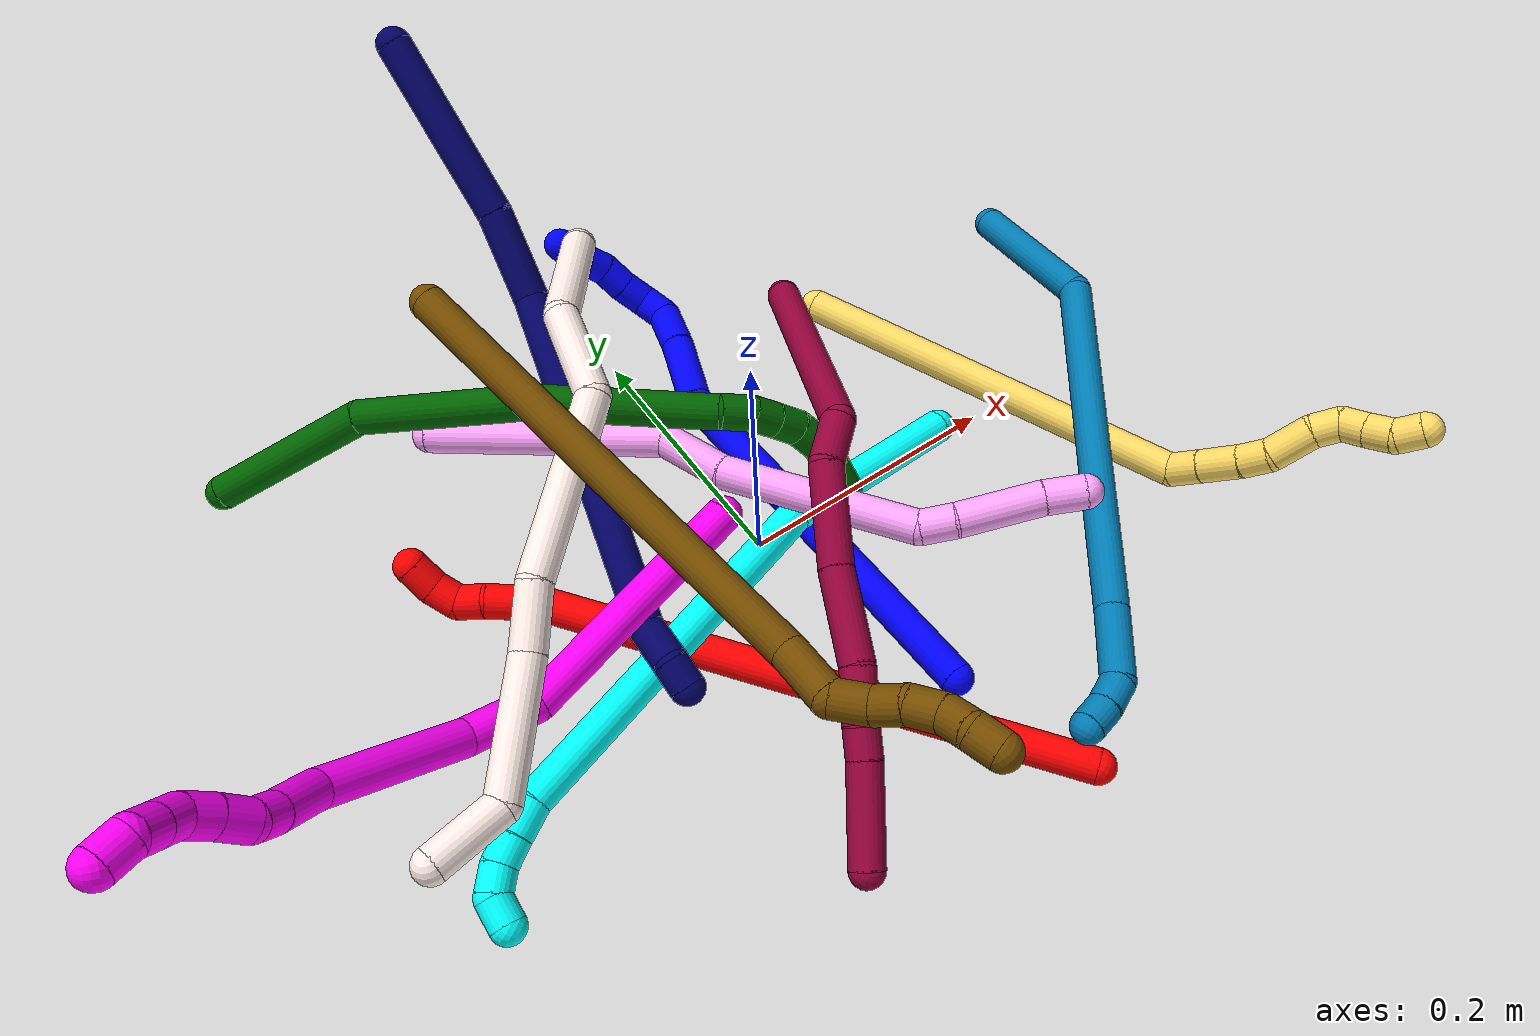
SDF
<sdf version="1.7">
 <world name="default">
  <plugin name="TubeGeneratorPlugin" filename="libtube_generator_plugin.so"/>
  <model name="photoneo_s_sensor">
   <static>1</static>
   <pose>0 0 2 1.57079 1.57079 3.14159</pose>
   <link name="link">
    <inertial><mass>0.1</mass></inertial>
    <sensor name="sensor" type="depth">
     <update_rate>30</update_rate>
     <camera>
      <horizontal_fov>1.22</horizontal_fov>
      <image><width>1920</width><height>1200</height><format>B8G8R8</format></image>
      <clip><near>0.1</near><far>4</far></clip>
      <depth_camera><output>points</output></depth_camera>
     </camera>
     <plugin name="camera_plugin" filename="libgazebo_ros_depth_camera.so">
      <baseline>0.2</baseline>
      <alwaysOn>1</alwaysOn>
      <updateRate>0.0</updateRate>
      <cameraName>camera_ir</cameraName>
      <imageTopicName>/camera/color/image_raw</imageTopicName>
      <cameraInfoTopicName>/camera/color/camera_info</cameraInfoTopicName>
      <depthImageTopicName>/camera/depth/image_raw</depthImageTopicName>
      <depthImageCameraInfoTopicName>/camera/depth/camera_info</depthImageCameraInfoTopicName>
      <pointCloudTopicName>/camera/depth/points</pointCloudTopicName>
      <frameName>fr_optical</frameName>
      <pointCloudCutoff>0.1</pointCloudCutoff>
      <pointCloudCutoffMax>2.0</pointCloudCutoffMax>
      <distortionK1>0</distortionK1>
      <distortionK2>0</distortionK2>
      <distortionK3>0</distortionK3>
      <distortionT1>0</distortionT1>
      <distortionT2>0</distortionT2>
      <CxPrime>0</CxPrime>
      <Cx>0</Cx>
      <Cy>0</Cy>
      <focalLength>0</focalLength>
      <hackBaseline>0</hackBaseline>
     </plugin>
    </sensor>
   </link>
  </model>
  <gravity>0 0 -9.8</gravity>
  <magnetic_field>6e-06 2.3e-05 -4.2e-05</magnetic_field>
  <atmosphere type="adiabatic"/>
  <physics name="default_physics" default="0" type="ode">
   <max_step_size>0.003</max_step_size>
   <real_time_factor>1</real_time_factor>
   <real_time_update_rate>1000</real_time_update_rate>
   <max_contacts>10000</max_contacts>
   <ode>
    <solver>
     <type>quick</type>
     <iters>100</iters>
     <sor>1.3</sor>
     <use_dynamic_moi_rescaling>0</use_dynamic_moi_rescaling>
    </solver>
    <constraints>
     <contact_max_correcting_vel>0</contact_max_correcting_vel>
     <contact_surface_layer>0.001</contact_surface_layer>
     <cfm>0</cfm>
     <erp>0.2</erp>
    </constraints>
   </ode>
  </physics>
  <scene><ambient>0.4 0.4 0.4 1</ambient><background>0.7 0.7 0.7 1</background><shadows>0</shadows></scene>
  <audio><device>default</device></audio>
  <spherical_coordinates>
   <surface_model>EARTH_WGS84</surface_model>
   <latitude_deg>0</latitude_deg>
   <longitude_deg>0</longitude_deg>
   <elevation>0</elevation>
   <heading_deg>0</heading_deg>
  </spherical_coordinates>
  <model name="bin">
   <static>1</static>
   <link name="bottom">
    <collision name="collision-bottom">
     <pose>0 0 -0.01 0 -0 0</pose>
     <geometry><box><size>0.8 0.6 0.02</size></box></geometry>
     <surface>
      <friction><ode><mu>100</mu><mu2>100</mu2></ode></friction>
      <contact><collide_bitmask>65535</collide_bitmask></contact>
     </surface>
    </collision>
   </link>
   <link name="west_wall">
    <collision name="collision-west_wall">
     <pose>-0.41 0 0.1 0 -0 0</pose>
     <geometry><box><size>0.02 0.6 0.2</size></box></geometry>
     <surface>
      <friction><ode><mu>100</mu><mu2>100</mu2></ode></friction>
      <contact><collide_bitmask>65535</collide_bitmask></contact>
     </surface>
    </collision>
   </link>
   <link name="east_wall">
    <collision name="collision-east_wall">
     <pose>0.41 0 0.1 0 -0 0</pose>
     <geometry><box><size>0.02 0.6 0.2</size></box></geometry>
     <surface>
      <friction><ode><mu>100</mu><mu2>100</mu2></ode></friction>
      <contact><collide_bitmask>65535</collide_bitmask></contact>
     </surface>
    </collision>
   </link>
   <link name="south_wall">
    <collision name="collision-south_wall">
     <pose>0 -0.31 0.1 0 -0 0</pose>
     <geometry><box><size>0.8 0.02 0.2</size></box></geometry>
     <surface>
      <friction><ode><mu>100</mu><mu2>100</mu2></ode></friction>
      <contact><collide_bitmask>65535</collide_bitmask></contact>
     </surface>
    </collision>
   </link>
   <link name="north_wall">
    <collision name="collision-north_wall">
     <pose>0 0.31 0.1 0 -0 0</pose>
     <geometry><box><size>0.8 0.02 0.2</size></box></geometry>
     <surface>
      <friction><ode><mu>100</mu><mu2>100</mu2></ode></friction>
      <contact><collide_bitmask>65535</collide_bitmask></contact>
     </surface>
    </collision>
   </link>
  </model>
  <model name="1">
   <static>0</static>
   <link name="1">
    <collision name="collision-cylinder-e_1_1_4">
     <pose>0.000756 0.152473 0.007462 -1.5219 0.004953 -0.004716</pose>
     <geometry><cylinder><radius>0.0125</radius><length>0.305315</length></cylinder></geometry>
     <surface>
      <friction><ode><mu>1.16</mu><mu2>1.16</mu2><slip1>0</slip1><slip2>0</slip2></ode></friction>
      <contact><ode><kp>1e+06</kp><kd>1</kd><max_vel>0</max_vel><min_depth>0.001</min_depth></ode></contact>
     </surface>
    </collision>
    <visual name="visual-cylinder-e_1_1_4">
     <pose>0.000756 0.152473 0.007462 -1.5219 0.004953 -0.004716</pose>
     <geometry><cylinder><radius>0.0125</radius><length>0.305315</length></cylinder></geometry>
     <material><ambient>0 0 1 1</ambient></material>
    </visual>
    <collision name="collision-cylinder-e_2_4_5">
     <pose>0.012253 0.331208 0.016992 -1.49217 0.387147 -0.358492</pose>
     <geometry><cylinder><radius>0.0125</radius><length>0.056898</length></cylinder></geometry>
     <surface>
      <friction><ode><mu>1.16</mu><mu2>1.16</mu2><slip1>0</slip1><slip2>0</slip2></ode></friction>
      <contact><ode><kp>1e+06</kp><kd>1</kd><max_vel>0</max_vel><min_depth>0.001</min_depth></ode></contact>
     </surface>
    </collision>
    <visual name="visual-cylinder-e_2_4_5">
     <pose>0.012253 0.331208 0.016992 -1.49217 0.387147 -0.358492</pose>
     <geometry><cylinder><radius>0.0125</radius><length>0.056898</length></cylinder></geometry>
     <material><ambient>0 0 1 1</ambient></material>
    </visual>
    <collision name="collision-cylinder-e_3_5_6">
     <pose>0.028045 0.373838 0.020113 -1.50663 0.298769 -0.280437</pose>
     <geometry><cylinder><radius>0.0125</radius><length>0.034323</length></cylinder></geometry>
     <surface>
      <friction><ode><mu>1.16</mu><mu2>1.16</mu2><slip1>0</slip1><slip2>0</slip2></ode></friction>
      <contact><ode><kp>1e+06</kp><kd>1</kd><max_vel>0</max_vel><min_depth>0.001</min_depth></ode></contact>
     </surface>
    </collision>
    <visual name="visual-cylinder-e_3_5_6">
     <pose>0.028045 0.373838 0.020113 -1.50663 0.298769 -0.280437</pose>
     <geometry><cylinder><radius>0.0125</radius><length>0.034323</length></cylinder></geometry>
     <material><ambient>0 0 1 1</ambient></material>
    </visual>
    <collision name="collision-cylinder-e_4_6_7">
     <pose>0.030387 0.400199 0.022974 -1.3917 -0.260783 0.218184</pose>
     <geometry><cylinder><radius>0.0125</radius><length>0.021022</length></cylinder></geometry>
     <surface>
      <friction><ode><mu>1.16</mu><mu2>1.16</mu2><slip1>0</slip1><slip2>0</slip2></ode></friction>
      <contact><ode><kp>1e+06</kp><kd>1</kd><max_vel>0</max_vel><min_depth>0.001</min_depth></ode></contact>
     </surface>
    </collision>
    <visual name="visual-cylinder-e_4_6_7">
     <pose>0.030387 0.400199 0.022974 -1.3917 -0.260783 0.218184</pose>
     <geometry><cylinder><radius>0.0125</radius><length>0.021022</length></cylinder></geometry>
     <material><ambient>0 0 1 1</ambient></material>
    </visual>
    <collision name="collision-cylinder-e_5_7_8">
     <pose>0.022226 0.416851 0.031117 -0.810451 -0.535341 0.234213</pose>
     <geometry><cylinder><radius>0.0125</radius><length>0.021369</length></cylinder></geometry>
     <surface>
      <friction><ode><mu>1.16</mu><mu2>1.16</mu2><slip1>0</slip1><slip2>0</slip2></ode></friction>
      <contact><ode><kp>1e+06</kp><kd>1</kd><max_vel>0</max_vel><min_depth>0.001</min_depth></ode></contact>
     </surface>
    </collision>
    <visual name="visual-cylinder-e_5_7_8">
     <pose>0.022226 0.416851 0.031117 -0.810451 -0.535341 0.234213</pose>
     <geometry><cylinder><radius>0.0125</radius><length>0.021369</length></cylinder></geometry>
     <material><ambient>0 0 1 1</ambient></material>
    </visual>
    <collision name="collision-cylinder-e_6_8_9">
     <pose>0.01266 0.429975 0.044131 -0.769032 -0.416754 0.170711</pose>
     <geometry><cylinder><radius>0.0125</radius><length>0.020335</length></cylinder></geometry>
     <surface>
      <friction><ode><mu>1.16</mu><mu2>1.16</mu2><slip1>0</slip1><slip2>0</slip2></ode></friction>
      <contact><ode><kp>1e+06</kp><kd>1</kd><max_vel>0</max_vel><min_depth>0.001</min_depth></ode></contact>
     </surface>
    </collision>
    <visual name="visual-cylinder-e_6_8_9">
     <pose>0.01266 0.429975 0.044131 -0.769032 -0.416754 0.170711</pose>
     <geometry><cylinder><radius>0.0125</radius><length>0.020335</length></cylinder></geometry>
     <material><ambient>0 0 1 1</ambient></material>
    </visual>
    <collision name="collision-cylinder-e_7_9_10">
     <pose>0.001447 0.440461 0.057068 -0.571053 -0.762047 0.234115</pose>
     <geometry><cylinder><radius>0.0125</radius><length>0.020558</length></cylinder></geometry>
     <surface>
      <friction><ode><mu>1.16</mu><mu2>1.16</mu2><slip1>0</slip1><slip2>0</slip2></ode></friction>
      <contact><ode><kp>1e+06</kp><kd>1</kd><max_vel>0</max_vel><min_depth>0.001</min_depth></ode></contact>
     </surface>
    </collision>
    <visual name="visual-cylinder-e_7_9_10">
     <pose>0.001447 0.440461 0.057068 -0.571053 -0.762047 0.234115</pose>
     <geometry><cylinder><radius>0.0125</radius><length>0.020558</length></cylinder></geometry>
     <material><ambient>0 0 1 1</ambient></material>
    </visual>
    <collision name="collision-cylinder-e_8_10_2">
     <pose>-0.011336 0.450059 0.069516 -0.733362 -0.598726 0.235964</pose>
     <geometry><cylinder><radius>0.0125</radius><length>0.020179</length></cylinder></geometry>
     <surface>
      <friction><ode><mu>1.16</mu><mu2>1.16</mu2><slip1>0</slip1><slip2>0</slip2></ode></friction>
      <contact><ode><kp>1e+06</kp><kd>1</kd><max_vel>0</max_vel><min_depth>0.001</min_depth></ode></contact>
     </surface>
    </collision>
    <visual name="visual-cylinder-e_8_10_2">
     <pose>-0.011336 0.450059 0.069516 -0.733362 -0.598726 0.235964</pose>
     <geometry><cylinder><radius>0.0125</radius><length>0.020179</length></cylinder></geometry>
     <material><ambient>0 0 1 1</ambient></material>
    </visual>
    <collision name="collision-sphere-2">
     <pose>-0.017022 0.455638 0.075708 0 -0 0</pose>
     <geometry><sphere><radius>0.0125</radius></sphere></geometry>
     <surface>
      <friction><ode><mu>1.16</mu><mu2>1.16</mu2><slip1>0</slip1><slip2>0</slip2></ode></friction>
      <contact><ode><kp>1e+06</kp><kd>1</kd><max_vel>0</max_vel><min_depth>0.001</min_depth></ode></contact>
     </surface>
    </collision>
    <visual name="visual-sphere-2">
     <pose>-0.017022 0.455638 0.075708 0 -0 0</pose>
     <geometry><sphere><radius>0.0125</radius></sphere></geometry>
     <material><ambient>0 0 1 1</ambient></material>
    </visual>
    <collision name="collision-sphere-10">
     <pose>-0.005649 0.44448 0.063324 0 -0 0</pose>
     <geometry><sphere><radius>0.0125</radius></sphere></geometry>
     <surface>
      <friction><ode><mu>1.16</mu><mu2>1.16</mu2><slip1>0</slip1><slip2>0</slip2></ode></friction>
      <contact><ode><kp>1e+06</kp><kd>1</kd><max_vel>0</max_vel><min_depth>0.001</min_depth></ode></contact>
     </surface>
    </collision>
    <visual name="visual-sphere-10">
     <pose>-0.005649 0.44448 0.063324 0 -0 0</pose>
     <geometry><sphere><radius>0.0125</radius></sphere></geometry>
     <material><ambient>0 0 1 1</ambient></material>
    </visual>
    <collision name="collision-sphere-9">
     <pose>0.008544 0.436441 0.050812 0 -0 0</pose>
     <geometry><sphere><radius>0.0125</radius></sphere></geometry>
     <surface>
      <friction><ode><mu>1.16</mu><mu2>1.16</mu2><slip1>0</slip1><slip2>0</slip2></ode></friction>
      <contact><ode><kp>1e+06</kp><kd>1</kd><max_vel>0</max_vel><min_depth>0.001</min_depth></ode></contact>
     </surface>
    </collision>
    <visual name="visual-sphere-9">
     <pose>0.008544 0.436441 0.050812 0 -0 0</pose>
     <geometry><sphere><radius>0.0125</radius></sphere></geometry>
     <material><ambient>0 0 1 1</ambient></material>
    </visual>
    <collision name="collision-sphere-4">
     <pose>0.001512 0.304946 0.014923 0 -0 0</pose>
     <geometry><sphere><radius>0.0125</radius></sphere></geometry>
     <surface>
      <friction><ode><mu>1.16</mu><mu2>1.16</mu2><slip1>0</slip1><slip2>0</slip2></ode></friction>
      <contact><ode><kp>1e+06</kp><kd>1</kd><max_vel>0</max_vel><min_depth>0.001</min_depth></ode></contact>
     </surface>
    </collision>
    <visual name="visual-sphere-4">
     <pose>0.001512 0.304946 0.014923 0 -0 0</pose>
     <geometry><sphere><radius>0.0125</radius></sphere></geometry>
     <material><ambient>0 0 1 1</ambient></material>
    </visual>
    <collision name="collision-sphere-1">
     <geometry><sphere><radius>0.0125</radius></sphere></geometry>
     <surface>
      <friction><ode><mu>1.16</mu><mu2>1.16</mu2><slip1>0</slip1><slip2>0</slip2></ode></friction>
      <contact><ode><kp>1e+06</kp><kd>1</kd><max_vel>0</max_vel><min_depth>0.001</min_depth></ode></contact>
     </surface>
    </collision>
    <visual name="visual-sphere-1">
     <geometry><sphere><radius>0.0125</radius></sphere></geometry>
     <material><ambient>0 0 1 1</ambient></material>
    </visual>
    <collision name="collision-sphere-8">
     <pose>0.016776 0.42351 0.03745 0 -0 0</pose>
     <geometry><sphere><radius>0.0125</radius></sphere></geometry>
     <surface>
      <friction><ode><mu>1.16</mu><mu2>1.16</mu2><slip1>0</slip1><slip2>0</slip2></ode></friction>
      <contact><ode><kp>1e+06</kp><kd>1</kd><max_vel>0</max_vel><min_depth>0.001</min_depth></ode></contact>
     </surface>
    </collision>
    <visual name="visual-sphere-8">
     <pose>0.016776 0.42351 0.03745 0 -0 0</pose>
     <geometry><sphere><radius>0.0125</radius></sphere></geometry>
     <material><ambient>0 0 1 1</ambient></material>
    </visual>
    <collision name="collision-sphere-5">
     <pose>0.022994 0.35747 0.019062 0 -0 0</pose>
     <geometry><sphere><radius>0.0125</radius></sphere></geometry>
     <surface>
      <friction><ode><mu>1.16</mu><mu2>1.16</mu2><slip1>0</slip1><slip2>0</slip2></ode></friction>
      <contact><ode><kp>1e+06</kp><kd>1</kd><max_vel>0</max_vel><min_depth>0.001</min_depth></ode></contact>
     </surface>
    </collision>
    <visual name="visual-sphere-5">
     <pose>0.022994 0.35747 0.019062 0 -0 0</pose>
     <geometry><sphere><radius>0.0125</radius></sphere></geometry>
     <material><ambient>0 0 1 1</ambient></material>
    </visual>
    <collision name="collision-sphere-6">
     <pose>0.033097 0.390206 0.021165 0 -0 0</pose>
     <geometry><sphere><radius>0.0125</radius></sphere></geometry>
     <surface>
      <friction><ode><mu>1.16</mu><mu2>1.16</mu2><slip1>0</slip1><slip2>0</slip2></ode></friction>
      <contact><ode><kp>1e+06</kp><kd>1</kd><max_vel>0</max_vel><min_depth>0.001</min_depth></ode></contact>
     </surface>
    </collision>
    <visual name="visual-sphere-6">
     <pose>0.033097 0.390206 0.021165 0 -0 0</pose>
     <geometry><sphere><radius>0.0125</radius></sphere></geometry>
     <material><ambient>0 0 1 1</ambient></material>
    </visual>
    <collision name="collision-sphere-7">
     <pose>0.027676 0.410192 0.024783 0 -0 0</pose>
     <geometry><sphere><radius>0.0125</radius></sphere></geometry>
     <surface>
      <friction><ode><mu>1.16</mu><mu2>1.16</mu2><slip1>0</slip1><slip2>0</slip2></ode></friction>
      <contact><ode><kp>1e+06</kp><kd>1</kd><max_vel>0</max_vel><min_depth>0.001</min_depth></ode></contact>
     </surface>
    </collision>
    <visual name="visual-sphere-7">
     <pose>0.027676 0.410192 0.024783 0 -0 0</pose>
     <geometry><sphere><radius>0.0125</radius></sphere></geometry>
     <material><ambient>0 0 1 1</ambient></material>
    </visual>
    <inertial>
     <pose>0.006126 0.24486 0.017113 0 -0 0</pose>
     <mass>0.5</mass>
     <inertia>
      <ixx>0.002392</ixx>
      <ixy>0</ixy>
      <ixz>0</ixz>
      <iyy>0.000145</iyy>
      <iyz>0</iyz>
      <izz>-0.002417</izz>
     </inertia>
    </inertial>
   </link>
   <pose>0.044102 -0.173826 0.011499 -0.047755 0.075582 0.04905</pose>
  </model>
  <model name="2">
   <static>0</static>
   <link name="2">
    <collision name="collision-cylinder-e_1_1_4">
     <pose>-0.114793 0.151228 -0.051001 -1.89606 -0.623542 0.843717</pose>
     <geometry><cylinder><radius>0.0125</radius><length>0.393184</length></cylinder></geometry>
     <surface>
      <friction><ode><mu>1.16</mu><mu2>1.16</mu2><slip1>0</slip1><slip2>0</slip2></ode></friction>
      <contact><ode><kp>1e+06</kp><kd>1</kd><max_vel>0</max_vel><min_depth>0.001</min_depth></ode></contact>
     </surface>
    </collision>
    <visual name="visual-cylinder-e_1_1_4">
     <pose>-0.114793 0.151228 -0.051001 -1.89606 -0.623542 0.843717</pose>
     <geometry><cylinder><radius>0.0125</radius><length>0.393184</length></cylinder></geometry>
     <material><ambient>1 0 0 1</ambient></material>
    </visual>
    <collision name="collision-cylinder-e_2_4_5">
     <pose>-0.237313 0.307981 -0.105901 -2.18526 -0.851849 1.43809</pose>
     <geometry><cylinder><radius>0.0125</radius><length>0.020537</length></cylinder></geometry>
     <surface>
      <friction><ode><mu>1.16</mu><mu2>1.16</mu2><slip1>0</slip1><slip2>0</slip2></ode></friction>
      <contact><ode><kp>1e+06</kp><kd>1</kd><max_vel>0</max_vel><min_depth>0.001</min_depth></ode></contact>
     </surface>
    </collision>
    <visual name="visual-cylinder-e_2_4_5">
     <pose>-0.237313 0.307981 -0.105901 -2.18526 -0.851849 1.43809</pose>
     <geometry><cylinder><radius>0.0125</radius><length>0.020537</length></cylinder></geometry>
     <material><ambient>1 0 0 1</ambient></material>
    </visual>
    <collision name="collision-cylinder-e_3_5_6">
     <pose>-0.253519 0.320119 -0.115137 -2.24992 -0.784323 1.4267</pose>
     <geometry><cylinder><radius>0.0125</radius><length>0.024009</length></cylinder></geometry>
     <surface>
      <friction><ode><mu>1.16</mu><mu2>1.16</mu2><slip1>0</slip1><slip2>0</slip2></ode></friction>
      <contact><ode><kp>1e+06</kp><kd>1</kd><max_vel>0</max_vel><min_depth>0.001</min_depth></ode></contact>
     </surface>
    </collision>
    <visual name="visual-cylinder-e_3_5_6">
     <pose>-0.253519 0.320119 -0.115137 -2.24992 -0.784323 1.4267</pose>
     <geometry><cylinder><radius>0.0125</radius><length>0.024009</length></cylinder></geometry>
     <material><ambient>1 0 0 1</ambient></material>
    </visual>
    <collision name="collision-cylinder-e_4_6_7">
     <pose>-0.267342 0.333269 -0.125981 -2.2708 -0.558699 1.10515</pose>
     <geometry><cylinder><radius>0.0125</radius><length>0.020163</length></cylinder></geometry>
     <surface>
      <friction><ode><mu>1.16</mu><mu2>1.16</mu2><slip1>0</slip1><slip2>0</slip2></ode></friction>
      <contact><ode><kp>1e+06</kp><kd>1</kd><max_vel>0</max_vel><min_depth>0.001</min_depth></ode></contact>
     </surface>
    </collision>
    <visual name="visual-cylinder-e_4_6_7">
     <pose>-0.267342 0.333269 -0.125981 -2.2708 -0.558699 1.10515</pose>
     <geometry><cylinder><radius>0.0125</radius><length>0.020163</length></cylinder></geometry>
     <material><ambient>1 0 0 1</ambient></material>
    </visual>
    <collision name="collision-cylinder-e_5_7_8">
     <pose>-0.280525 0.346243 -0.131106 -1.51145 -0.882552 0.837561</pose>
     <geometry><cylinder><radius>0.0125</radius><length>0.020298</length></cylinder></geometry>
     <surface>
      <friction><ode><mu>1.16</mu><mu2>1.16</mu2><slip1>0</slip1><slip2>0</slip2></ode></friction>
      <contact><ode><kp>1e+06</kp><kd>1</kd><max_vel>0</max_vel><min_depth>0.001</min_depth></ode></contact>
     </surface>
    </collision>
    <visual name="visual-cylinder-e_5_7_8">
     <pose>-0.280525 0.346243 -0.131106 -1.51145 -0.882552 0.837561</pose>
     <geometry><cylinder><radius>0.0125</radius><length>0.020298</length></cylinder></geometry>
     <material><ambient>1 0 0 1</ambient></material>
    </visual>
    <collision name="collision-cylinder-e_6_8_2">
     <pose>-0.297496 0.357629 -0.127406 -0.980392 -0.992638 0.562639</pose>
     <geometry><cylinder><radius>0.0125</radius><length>0.02181</length></cylinder></geometry>
     <surface>
      <friction><ode><mu>1.16</mu><mu2>1.16</mu2><slip1>0</slip1><slip2>0</slip2></ode></friction>
      <contact><ode><kp>1e+06</kp><kd>1</kd><max_vel>0</max_vel><min_depth>0.001</min_depth></ode></contact>
     </surface>
    </collision>
    <visual name="visual-cylinder-e_6_8_2">
     <pose>-0.297496 0.357629 -0.127406 -0.980392 -0.992638 0.562639</pose>
     <geometry><cylinder><radius>0.0125</radius><length>0.02181</length></cylinder></geometry>
     <material><ambient>1 0 0 1</ambient></material>
    </visual>
    <collision name="collision-sphere-2">
     <pose>-0.306629 0.362579 -0.124088 0 -0 0</pose>
     <geometry><sphere><radius>0.0125</radius></sphere></geometry>
     <surface>
      <friction><ode><mu>1.16</mu><mu2>1.16</mu2><slip1>0</slip1><slip2>0</slip2></ode></friction>
      <contact><ode><kp>1e+06</kp><kd>1</kd><max_vel>0</max_vel><min_depth>0.001</min_depth></ode></contact>
     </surface>
    </collision>
    <visual name="visual-sphere-2">
     <pose>-0.306629 0.362579 -0.124088 0 -0 0</pose>
     <geometry><sphere><radius>0.0125</radius></sphere></geometry>
     <material><ambient>1 0 0 1</ambient></material>
    </visual>
    <collision name="collision-sphere-4">
     <pose>-0.229586 0.302456 -0.102002 0 -0 0</pose>
     <geometry><sphere><radius>0.0125</radius></sphere></geometry>
     <surface>
      <friction><ode><mu>1.16</mu><mu2>1.16</mu2><slip1>0</slip1><slip2>0</slip2></ode></friction>
      <contact><ode><kp>1e+06</kp><kd>1</kd><max_vel>0</max_vel><min_depth>0.001</min_depth></ode></contact>
     </surface>
    </collision>
    <visual name="visual-sphere-4">
     <pose>-0.229586 0.302456 -0.102002 0 -0 0</pose>
     <geometry><sphere><radius>0.0125</radius></sphere></geometry>
     <material><ambient>1 0 0 1</ambient></material>
    </visual>
    <collision name="collision-sphere-1">
     <geometry><sphere><radius>0.0125</radius></sphere></geometry>
     <surface>
      <friction><ode><mu>1.16</mu><mu2>1.16</mu2><slip1>0</slip1><slip2>0</slip2></ode></friction>
      <contact><ode><kp>1e+06</kp><kd>1</kd><max_vel>0</max_vel><min_depth>0.001</min_depth></ode></contact>
     </surface>
    </collision>
    <visual name="visual-sphere-1">
     <geometry><sphere><radius>0.0125</radius></sphere></geometry>
     <material><ambient>1 0 0 1</ambient></material>
    </visual>
    <collision name="collision-sphere-8">
     <pose>-0.288363 0.352678 -0.130724 0 -0 0</pose>
     <geometry><sphere><radius>0.0125</radius></sphere></geometry>
     <surface>
      <friction><ode><mu>1.16</mu><mu2>1.16</mu2><slip1>0</slip1><slip2>0</slip2></ode></friction>
      <contact><ode><kp>1e+06</kp><kd>1</kd><max_vel>0</max_vel><min_depth>0.001</min_depth></ode></contact>
     </surface>
    </collision>
    <visual name="visual-sphere-8">
     <pose>-0.288363 0.352678 -0.130724 0 -0 0</pose>
     <geometry><sphere><radius>0.0125</radius></sphere></geometry>
     <material><ambient>1 0 0 1</ambient></material>
    </visual>
    <collision name="collision-sphere-5">
     <pose>-0.24504 0.313507 -0.109799 0 -0 0</pose>
     <geometry><sphere><radius>0.0125</radius></sphere></geometry>
     <surface>
      <friction><ode><mu>1.16</mu><mu2>1.16</mu2><slip1>0</slip1><slip2>0</slip2></ode></friction>
      <contact><ode><kp>1e+06</kp><kd>1</kd><max_vel>0</max_vel><min_depth>0.001</min_depth></ode></contact>
     </surface>
    </collision>
    <visual name="visual-sphere-5">
     <pose>-0.24504 0.313507 -0.109799 0 -0 0</pose>
     <geometry><sphere><radius>0.0125</radius></sphere></geometry>
     <material><ambient>1 0 0 1</ambient></material>
    </visual>
    <collision name="collision-sphere-6">
     <pose>-0.261998 0.326731 -0.120474 0 -0 0</pose>
     <geometry><sphere><radius>0.0125</radius></sphere></geometry>
     <surface>
      <friction><ode><mu>1.16</mu><mu2>1.16</mu2><slip1>0</slip1><slip2>0</slip2></ode></friction>
      <contact><ode><kp>1e+06</kp><kd>1</kd><max_vel>0</max_vel><min_depth>0.001</min_depth></ode></contact>
     </surface>
    </collision>
    <visual name="visual-sphere-6">
     <pose>-0.261998 0.326731 -0.120474 0 -0 0</pose>
     <geometry><sphere><radius>0.0125</radius></sphere></geometry>
     <material><ambient>1 0 0 1</ambient></material>
    </visual>
    <collision name="collision-sphere-7">
     <pose>-0.272686 0.339808 -0.131488 0 -0 0</pose>
     <geometry><sphere><radius>0.0125</radius></sphere></geometry>
     <surface>
      <friction><ode><mu>1.16</mu><mu2>1.16</mu2><slip1>0</slip1><slip2>0</slip2></ode></friction>
      <contact><ode><kp>1e+06</kp><kd>1</kd><max_vel>0</max_vel><min_depth>0.001</min_depth></ode></contact>
     </surface>
    </collision>
    <visual name="visual-sphere-7">
     <pose>-0.272686 0.339808 -0.131488 0 -0 0</pose>
     <geometry><sphere><radius>0.0125</radius></sphere></geometry>
     <material><ambient>1 0 0 1</ambient></material>
    </visual>
    <inertial>
     <pose>-0.147336 0.190037 -0.065944 0 -0 0</pose>
     <mass>0.5</mass>
     <inertia>
      <ixx>0.005806</ixx>
      <ixy>0</ixy>
      <ixz>0</ixz>
      <iyy>0.00414</iyy>
      <iyz>0</iyz>
      <izz>-0.00095</izz>
     </inertia>
    </inertial>
   </link>
   <pose>0.079198 -0.279915 0.011496 -0.588276 0.833262 -0.420484</pose>
  </model>
  <model name="3">
   <static>0</static>
   <link name="3">
    <collision name="collision-cylinder-e_1_1_4">
     <pose>-0.060567 -0.016771 0.034482 0.452682 -1.0064 -0.252184</pose>
     <geometry><cylinder><radius>0.0125</radius><length>0.14337</length></cylinder></geometry>
     <surface>
      <friction><ode><mu>1.16</mu><mu2>1.16</mu2><slip1>0</slip1><slip2>0</slip2></ode></friction>
      <contact><ode><kp>1e+06</kp><kd>1</kd><max_vel>0</max_vel><min_depth>0.001</min_depth></ode></contact>
     </surface>
    </collision>
    <visual name="visual-cylinder-e_1_1_4">
     <pose>-0.060567 -0.016771 0.034482 0.452682 -1.0064 -0.252184</pose>
     <geometry><cylinder><radius>0.0125</radius><length>0.14337</length></cylinder></geometry>
     <material><ambient>0.003922 1 0.996078 1</ambient></material>
    </visual>
    <collision name="collision-cylinder-e_2_4_5">
     <pose>-0.249768 -0.059769 0.104105 0.641159 -1.24227 -0.466571</pose>
     <geometry><cylinder><radius>0.0125</radius><length>0.271803</length></cylinder></geometry>
     <surface>
      <friction><ode><mu>1.16</mu><mu2>1.16</mu2><slip1>0</slip1><slip2>0</slip2></ode></friction>
      <contact><ode><kp>1e+06</kp><kd>1</kd><max_vel>0</max_vel><min_depth>0.001</min_depth></ode></contact>
     </surface>
    </collision>
    <visual name="visual-cylinder-e_2_4_5">
     <pose>-0.249768 -0.059769 0.104105 0.641159 -1.24227 -0.466571</pose>
     <geometry><cylinder><radius>0.0125</radius><length>0.271803</length></cylinder></geometry>
     <material><ambient>0.003922 1 0.996078 1</ambient></material>
    </visual>
    <collision name="collision-cylinder-e_3_5_6">
     <pose>-0.39043 -0.087977 0.139385 1.50026 -1.40711 -1.33791</pose>
     <geometry><cylinder><radius>0.0125</radius><length>0.024383</length></cylinder></geometry>
     <surface>
      <friction><ode><mu>1.16</mu><mu2>1.16</mu2><slip1>0</slip1><slip2>0</slip2></ode></friction>
      <contact><ode><kp>1e+06</kp><kd>1</kd><max_vel>0</max_vel><min_depth>0.001</min_depth></ode></contact>
     </surface>
    </collision>
    <visual name="visual-cylinder-e_3_5_6">
     <pose>-0.39043 -0.087977 0.139385 1.50026 -1.40711 -1.33791</pose>
     <geometry><cylinder><radius>0.0125</radius><length>0.024383</length></cylinder></geometry>
     <material><ambient>0.003922 1 0.996078 1</ambient></material>
    </visual>
    <collision name="collision-cylinder-e_4_6_7">
     <pose>-0.412574 -0.091015 0.139197 1.87142 -1.46193 -1.76573</pose>
     <geometry><cylinder><radius>0.0125</radius><length>0.020351</length></cylinder></geometry>
     <surface>
      <friction><ode><mu>1.16</mu><mu2>1.16</mu2><slip1>0</slip1><slip2>0</slip2></ode></friction>
      <contact><ode><kp>1e+06</kp><kd>1</kd><max_vel>0</max_vel><min_depth>0.001</min_depth></ode></contact>
     </surface>
    </collision>
    <visual name="visual-cylinder-e_4_6_7">
     <pose>-0.412574 -0.091015 0.139197 1.87142 -1.46193 -1.76573</pose>
     <geometry><cylinder><radius>0.0125</radius><length>0.020351</length></cylinder></geometry>
     <material><ambient>0.003922 1 0.996078 1</ambient></material>
    </visual>
    <collision name="collision-cylinder-e_5_7_8">
     <pose>-0.431765 -0.095316 0.13608 2.28088 -1.13019 -1.88832</pose>
     <geometry><cylinder><radius>0.0125</radius><length>0.020068</length></cylinder></geometry>
     <surface>
      <friction><ode><mu>1.16</mu><mu2>1.16</mu2><slip1>0</slip1><slip2>0</slip2></ode></friction>
      <contact><ode><kp>1e+06</kp><kd>1</kd><max_vel>0</max_vel><min_depth>0.001</min_depth></ode></contact>
     </surface>
    </collision>
    <visual name="visual-cylinder-e_5_7_8">
     <pose>-0.431765 -0.095316 0.13608 2.28088 -1.13019 -1.88832</pose>
     <geometry><cylinder><radius>0.0125</radius><length>0.020068</length></cylinder></geometry>
     <material><ambient>0.003922 1 0.996078 1</ambient></material>
    </visual>
    <collision name="collision-cylinder-e_6_8_2">
     <pose>-0.446183 -0.100691 0.125094 2.88731 -0.562835 -2.30892</pose>
     <geometry><cylinder><radius>0.0125</radius><length>0.020026</length></cylinder></geometry>
     <surface>
      <friction><ode><mu>1.16</mu><mu2>1.16</mu2><slip1>0</slip1><slip2>0</slip2></ode></friction>
      <contact><ode><kp>1e+06</kp><kd>1</kd><max_vel>0</max_vel><min_depth>0.001</min_depth></ode></contact>
     </surface>
    </collision>
    <visual name="visual-cylinder-e_6_8_2">
     <pose>-0.446183 -0.100691 0.125094 2.88731 -0.562835 -2.30892</pose>
     <geometry><cylinder><radius>0.0125</radius><length>0.020026</length></cylinder></geometry>
     <material><ambient>0.003922 1 0.996078 1</ambient></material>
    </visual>
    <collision name="collision-sphere-2">
     <pose>-0.451526 -0.102821 0.116898 0 -0 0</pose>
     <geometry><sphere><radius>0.0125</radius></sphere></geometry>
     <surface>
      <friction><ode><mu>1.16</mu><mu2>1.16</mu2><slip1>0</slip1><slip2>0</slip2></ode></friction>
      <contact><ode><kp>1e+06</kp><kd>1</kd><max_vel>0</max_vel><min_depth>0.001</min_depth></ode></contact>
     </surface>
    </collision>
    <visual name="visual-sphere-2">
     <pose>-0.451526 -0.102821 0.116898 0 -0 0</pose>
     <geometry><sphere><radius>0.0125</radius></sphere></geometry>
     <material><ambient>0.003922 1 0.996078 1</ambient></material>
    </visual>
    <collision name="collision-sphere-4">
     <pose>-0.121135 -0.033542 0.068965 0 -0 0</pose>
     <geometry><sphere><radius>0.0125</radius></sphere></geometry>
     <surface>
      <friction><ode><mu>1.16</mu><mu2>1.16</mu2><slip1>0</slip1><slip2>0</slip2></ode></friction>
      <contact><ode><kp>1e+06</kp><kd>1</kd><max_vel>0</max_vel><min_depth>0.001</min_depth></ode></contact>
     </surface>
    </collision>
    <visual name="visual-sphere-4">
     <pose>-0.121135 -0.033542 0.068965 0 -0 0</pose>
     <geometry><sphere><radius>0.0125</radius></sphere></geometry>
     <material><ambient>0.003922 1 0.996078 1</ambient></material>
    </visual>
    <collision name="collision-sphere-1">
     <geometry><sphere><radius>0.0125</radius></sphere></geometry>
     <surface>
      <friction><ode><mu>1.16</mu><mu2>1.16</mu2><slip1>0</slip1><slip2>0</slip2></ode></friction>
      <contact><ode><kp>1e+06</kp><kd>1</kd><max_vel>0</max_vel><min_depth>0.001</min_depth></ode></contact>
     </surface>
    </collision>
    <visual name="visual-sphere-1">
     <geometry><sphere><radius>0.0125</radius></sphere></geometry>
     <material><ambient>0.003922 1 0.996078 1</ambient></material>
    </visual>
    <collision name="collision-sphere-8">
     <pose>-0.44084 -0.098561 0.13329 0 -0 0</pose>
     <geometry><sphere><radius>0.0125</radius></sphere></geometry>
     <surface>
      <friction><ode><mu>1.16</mu><mu2>1.16</mu2><slip1>0</slip1><slip2>0</slip2></ode></friction>
      <contact><ode><kp>1e+06</kp><kd>1</kd><max_vel>0</max_vel><min_depth>0.001</min_depth></ode></contact>
     </surface>
    </collision>
    <visual name="visual-sphere-8">
     <pose>-0.44084 -0.098561 0.13329 0 -0 0</pose>
     <geometry><sphere><radius>0.0125</radius></sphere></geometry>
     <material><ambient>0.003922 1 0.996078 1</ambient></material>
    </visual>
    <collision name="collision-sphere-5">
     <pose>-0.378402 -0.085995 0.139245 0 -0 0</pose>
     <geometry><sphere><radius>0.0125</radius></sphere></geometry>
     <surface>
      <friction><ode><mu>1.16</mu><mu2>1.16</mu2><slip1>0</slip1><slip2>0</slip2></ode></friction>
      <contact><ode><kp>1e+06</kp><kd>1</kd><max_vel>0</max_vel><min_depth>0.001</min_depth></ode></contact>
     </surface>
    </collision>
    <visual name="visual-sphere-5">
     <pose>-0.378402 -0.085995 0.139245 0 -0 0</pose>
     <geometry><sphere><radius>0.0125</radius></sphere></geometry>
     <material><ambient>0.003922 1 0.996078 1</ambient></material>
    </visual>
    <collision name="collision-sphere-6">
     <pose>-0.402459 -0.089959 0.139525 0 -0 0</pose>
     <geometry><sphere><radius>0.0125</radius></sphere></geometry>
     <surface>
      <friction><ode><mu>1.16</mu><mu2>1.16</mu2><slip1>0</slip1><slip2>0</slip2></ode></friction>
      <contact><ode><kp>1e+06</kp><kd>1</kd><max_vel>0</max_vel><min_depth>0.001</min_depth></ode></contact>
     </surface>
    </collision>
    <visual name="visual-sphere-6">
     <pose>-0.402459 -0.089959 0.139525 0 -0 0</pose>
     <geometry><sphere><radius>0.0125</radius></sphere></geometry>
     <material><ambient>0.003922 1 0.996078 1</ambient></material>
    </visual>
    <collision name="collision-sphere-7">
     <pose>-0.422689 -0.092071 0.13887 0 -0 0</pose>
     <geometry><sphere><radius>0.0125</radius></sphere></geometry>
     <surface>
      <friction><ode><mu>1.16</mu><mu2>1.16</mu2><slip1>0</slip1><slip2>0</slip2></ode></friction>
      <contact><ode><kp>1e+06</kp><kd>1</kd><max_vel>0</max_vel><min_depth>0.001</min_depth></ode></contact>
     </surface>
    </collision>
    <visual name="visual-sphere-7">
     <pose>-0.422689 -0.092071 0.13887 0 -0 0</pose>
     <geometry><sphere><radius>0.0125</radius></sphere></geometry>
     <material><ambient>0.003922 1 0.996078 1</ambient></material>
    </visual>
    <inertial>
     <pose>-0.224174 -0.053153 0.089414 0 -0 0</pose>
     <mass>0.5</mass>
     <inertia>
      <ixx>0.000299</ixx>
      <ixy>0</ixy>
      <ixz>0</ixz>
      <iyy>0.001594</iyy>
      <iyz>0</iyz>
      <izz>0.002206</izz>
     </inertia>
    </inertial>
   </link>
   <pose>0.163114 -0.000919 0.018719 -1.13997 -0.31226 0.449135</pose>
  </model>
  <model name="4">
   <static>0</static>
   <link name="4">
    <collision name="collision-cylinder-e_1_1_4">
     <pose>0.069429 -0.000526 0.059388 0.008852 0.863171 0.004077</pose>
     <geometry><cylinder><radius>0.0125</radius><length>0.18273</length></cylinder></geometry>
     <surface>
      <friction><ode><mu>1.16</mu><mu2>1.16</mu2><slip1>0</slip1><slip2>0</slip2></ode></friction>
      <contact><ode><kp>1e+06</kp><kd>1</kd><max_vel>0</max_vel><min_depth>0.001</min_depth></ode></contact>
     </surface>
    </collision>
    <visual name="visual-cylinder-e_1_1_4">
     <pose>0.069429 -0.000526 0.059388 0.008852 0.863171 0.004077</pose>
     <geometry><cylinder><radius>0.0125</radius><length>0.18273</length></cylinder></geometry>
     <material><ambient>1 0.65098 0.996078 1</ambient></material>
    </visual>
    <collision name="collision-cylinder-e_2_4_5">
     <pose>0.152251 -0.011666 0.137814 0.508608 0.550959 0.146684</pose>
     <geometry><cylinder><radius>0.0125</radius><length>0.051167</length></cylinder></geometry>
     <surface>
      <friction><ode><mu>1.16</mu><mu2>1.16</mu2><slip1>0</slip1><slip2>0</slip2></ode></friction>
      <contact><ode><kp>1e+06</kp><kd>1</kd><max_vel>0</max_vel><min_depth>0.001</min_depth></ode></contact>
     </surface>
    </collision>
    <visual name="visual-cylinder-e_2_4_5">
     <pose>0.152251 -0.011666 0.137814 0.508608 0.550959 0.146684</pose>
     <geometry><cylinder><radius>0.0125</radius><length>0.051167</length></cylinder></geometry>
     <material><ambient>1 0.65098 0.996078 1</ambient></material>
    </visual>
    <collision name="collision-cylinder-e_3_5_6">
     <pose>0.213329 -0.039301 0.21187 0.300034 0.691589 0.108804</pose>
     <geometry><cylinder><radius>0.0125</radius><length>0.149539</length></cylinder></geometry>
     <surface>
      <friction><ode><mu>1.16</mu><mu2>1.16</mu2><slip1>0</slip1><slip2>0</slip2></ode></friction>
      <contact><ode><kp>1e+06</kp><kd>1</kd><max_vel>0</max_vel><min_depth>0.001</min_depth></ode></contact>
     </surface>
    </collision>
    <visual name="visual-cylinder-e_3_5_6">
     <pose>0.213329 -0.039301 0.21187 0.300034 0.691589 0.108804</pose>
     <geometry><cylinder><radius>0.0125</radius><length>0.149539</length></cylinder></geometry>
     <material><ambient>1 0.65098 0.996078 1</ambient></material>
    </visual>
    <collision name="collision-cylinder-e_4_6_7">
     <pose>0.271293 -0.053797 0.2738 -0.350276 0.949383 -0.181365</pose>
     <geometry><cylinder><radius>0.0125</radius><length>0.025283</length></cylinder></geometry>
     <surface>
      <friction><ode><mu>1.16</mu><mu2>1.16</mu2><slip1>0</slip1><slip2>0</slip2></ode></friction>
      <contact><ode><kp>1e+06</kp><kd>1</kd><max_vel>0</max_vel><min_depth>0.001</min_depth></ode></contact>
     </surface>
    </collision>
    <visual name="visual-cylinder-e_4_6_7">
     <pose>0.271293 -0.053797 0.2738 -0.350276 0.949383 -0.181365</pose>
     <geometry><cylinder><radius>0.0125</radius><length>0.025283</length></cylinder></geometry>
     <material><ambient>1 0.65098 0.996078 1</ambient></material>
    </visual>
    <collision name="collision-cylinder-e_5_7_8">
     <pose>0.309022 -0.043868 0.293018 -0.54164 1.08879 -0.333067</pose>
     <geometry><cylinder><radius>0.0125</radius><length>0.06196</length></cylinder></geometry>
     <surface>
      <friction><ode><mu>1.16</mu><mu2>1.16</mu2><slip1>0</slip1><slip2>0</slip2></ode></friction>
      <contact><ode><kp>1e+06</kp><kd>1</kd><max_vel>0</max_vel><min_depth>0.001</min_depth></ode></contact>
     </surface>
    </collision>
    <visual name="visual-cylinder-e_5_7_8">
     <pose>0.309022 -0.043868 0.293018 -0.54164 1.08879 -0.333067</pose>
     <geometry><cylinder><radius>0.0125</radius><length>0.06196</length></cylinder></geometry>
     <material><ambient>1 0.65098 0.996078 1</ambient></material>
    </visual>
    <collision name="collision-cylinder-e_6_8_2">
     <pose>0.349063 -0.034323 0.312522 -0.289057 1.03297 -0.164934</pose>
     <geometry><cylinder><radius>0.0125</radius><length>0.029321</length></cylinder></geometry>
     <surface>
      <friction><ode><mu>1.16</mu><mu2>1.16</mu2><slip1>0</slip1><slip2>0</slip2></ode></friction>
      <contact><ode><kp>1e+06</kp><kd>1</kd><max_vel>0</max_vel><min_depth>0.001</min_depth></ode></contact>
     </surface>
    </collision>
    <visual name="visual-cylinder-e_6_8_2">
     <pose>0.349063 -0.034323 0.312522 -0.289057 1.03297 -0.164934</pose>
     <geometry><cylinder><radius>0.0125</radius><length>0.029321</length></cylinder></geometry>
     <material><ambient>1 0.65098 0.996078 1</ambient></material>
    </visual>
    <collision name="collision-sphere-2">
     <pose>0.361653 -0.032182 0.319721 0 -0 0</pose>
     <geometry><sphere><radius>0.0125</radius></sphere></geometry>
     <surface>
      <friction><ode><mu>1.16</mu><mu2>1.16</mu2><slip1>0</slip1><slip2>0</slip2></ode></friction>
      <contact><ode><kp>1e+06</kp><kd>1</kd><max_vel>0</max_vel><min_depth>0.001</min_depth></ode></contact>
     </surface>
    </collision>
    <visual name="visual-sphere-2">
     <pose>0.361653 -0.032182 0.319721 0 -0 0</pose>
     <geometry><sphere><radius>0.0125</radius></sphere></geometry>
     <material><ambient>1 0.65098 0.996078 1</ambient></material>
    </visual>
    <collision name="collision-sphere-4">
     <pose>0.138858 -0.001051 0.118776 0 -0 0</pose>
     <geometry><sphere><radius>0.0125</radius></sphere></geometry>
     <surface>
      <friction><ode><mu>1.16</mu><mu2>1.16</mu2><slip1>0</slip1><slip2>0</slip2></ode></friction>
      <contact><ode><kp>1e+06</kp><kd>1</kd><max_vel>0</max_vel><min_depth>0.001</min_depth></ode></contact>
     </surface>
    </collision>
    <visual name="visual-sphere-4">
     <pose>0.138858 -0.001051 0.118776 0 -0 0</pose>
     <geometry><sphere><radius>0.0125</radius></sphere></geometry>
     <material><ambient>1 0.65098 0.996078 1</ambient></material>
    </visual>
    <collision name="collision-sphere-1">
     <geometry><sphere><radius>0.0125</radius></sphere></geometry>
     <surface>
      <friction><ode><mu>1.16</mu><mu2>1.16</mu2><slip1>0</slip1><slip2>0</slip2></ode></friction>
      <contact><ode><kp>1e+06</kp><kd>1</kd><max_vel>0</max_vel><min_depth>0.001</min_depth></ode></contact>
     </surface>
    </collision>
    <visual name="visual-sphere-1">
     <geometry><sphere><radius>0.0125</radius></sphere></geometry>
     <material><ambient>1 0.65098 0.996078 1</ambient></material>
    </visual>
    <collision name="collision-sphere-8">
     <pose>0.336472 -0.036464 0.305324 0 -0 0</pose>
     <geometry><sphere><radius>0.0125</radius></sphere></geometry>
     <surface>
      <friction><ode><mu>1.16</mu><mu2>1.16</mu2><slip1>0</slip1><slip2>0</slip2></ode></friction>
      <contact><ode><kp>1e+06</kp><kd>1</kd><max_vel>0</max_vel><min_depth>0.001</min_depth></ode></contact>
     </surface>
    </collision>
    <visual name="visual-sphere-8">
     <pose>0.336472 -0.036464 0.305324 0 -0 0</pose>
     <geometry><sphere><radius>0.0125</radius></sphere></geometry>
     <material><ambient>1 0.65098 0.996078 1</ambient></material>
    </visual>
    <collision name="collision-sphere-5">
     <pose>0.165644 -0.022281 0.156853 0 -0 0</pose>
     <geometry><sphere><radius>0.0125</radius></sphere></geometry>
     <surface>
      <friction><ode><mu>1.16</mu><mu2>1.16</mu2><slip1>0</slip1><slip2>0</slip2></ode></friction>
      <contact><ode><kp>1e+06</kp><kd>1</kd><max_vel>0</max_vel><min_depth>0.001</min_depth></ode></contact>
     </surface>
    </collision>
    <visual name="visual-sphere-5">
     <pose>0.165644 -0.022281 0.156853 0 -0 0</pose>
     <geometry><sphere><radius>0.0125</radius></sphere></geometry>
     <material><ambient>1 0.65098 0.996078 1</ambient></material>
    </visual>
    <collision name="collision-sphere-6">
     <pose>0.261014 -0.056322 0.266887 0 -0 0</pose>
     <geometry><sphere><radius>0.0125</radius></sphere></geometry>
     <surface>
      <friction><ode><mu>1.16</mu><mu2>1.16</mu2><slip1>0</slip1><slip2>0</slip2></ode></friction>
      <contact><ode><kp>1e+06</kp><kd>1</kd><max_vel>0</max_vel><min_depth>0.001</min_depth></ode></contact>
     </surface>
    </collision>
    <visual name="visual-sphere-6">
     <pose>0.261014 -0.056322 0.266887 0 -0 0</pose>
     <geometry><sphere><radius>0.0125</radius></sphere></geometry>
     <material><ambient>1 0.65098 0.996078 1</ambient></material>
    </visual>
    <collision name="collision-sphere-7">
     <pose>0.281571 -0.051271 0.280713 0 -0 0</pose>
     <geometry><sphere><radius>0.0125</radius></sphere></geometry>
     <surface>
      <friction><ode><mu>1.16</mu><mu2>1.16</mu2><slip1>0</slip1><slip2>0</slip2></ode></friction>
      <contact><ode><kp>1e+06</kp><kd>1</kd><max_vel>0</max_vel><min_depth>0.001</min_depth></ode></contact>
     </surface>
    </collision>
    <visual name="visual-sphere-7">
     <pose>0.281571 -0.051271 0.280713 0 -0 0</pose>
     <geometry><sphere><radius>0.0125</radius></sphere></geometry>
     <material><ambient>1 0.65098 0.996078 1</ambient></material>
    </visual>
    <inertial>
     <pose>0.177238 -0.023309 0.167655 0 -0 0</pose>
     <mass>0.5</mass>
     <inertia>
      <ixx>0.000628</ixx>
      <ixy>0</ixy>
      <ixz>0</ixz>
      <iyy>0.000851</iyy>
      <iyz>0</iyz>
      <izz>-0.000513</izz>
     </inertia>
    </inertial>
   </link>
   <pose>-0.15458 0.206914 0.027983 0.777547 0.377371 -0.27014</pose>
  </model>
  <model name="5">
   <static>0</static>
   <link name="5">
    <collision name="collision-cylinder-e_1_1_4">
     <pose>0.011786 -0.065314 0.139741 0.437221 0.07626 0.01695</pose>
     <geometry><cylinder><radius>0.0125</radius><length>0.309401</length></cylinder></geometry>
     <surface>
      <friction><ode><mu>1.16</mu><mu2>1.16</mu2><slip1>0</slip1><slip2>0</slip2></ode></friction>
      <contact><ode><kp>1e+06</kp><kd>1</kd><max_vel>0</max_vel><min_depth>0.001</min_depth></ode></contact>
     </surface>
    </collision>
    <visual name="visual-cylinder-e_1_1_4">
     <pose>0.011786 -0.065314 0.139741 0.437221 0.07626 0.01695</pose>
     <geometry><cylinder><radius>0.0125</radius><length>0.309401</length></cylinder></geometry>
     <material><ambient>1 0.858824 0.4 1</ambient></material>
    </visual>
    <collision name="collision-cylinder-e_2_4_5">
     <pose>0.027344 -0.140389 0.285505 1.01797 0.317723 0.178331</pose>
     <geometry><cylinder><radius>0.0125</radius><length>0.024149</length></cylinder></geometry>
     <surface>
      <friction><ode><mu>1.16</mu><mu2>1.16</mu2><slip1>0</slip1><slip2>0</slip2></ode></friction>
      <contact><ode><kp>1e+06</kp><kd>1</kd><max_vel>0</max_vel><min_depth>0.001</min_depth></ode></contact>
     </surface>
    </collision>
    <visual name="visual-cylinder-e_2_4_5">
     <pose>0.027344 -0.140389 0.285505 1.01797 0.317723 0.178331</pose>
     <geometry><cylinder><radius>0.0125</radius><length>0.024149</length></cylinder></geometry>
     <material><ambient>1 0.858824 0.4 1</ambient></material>
    </visual>
    <collision name="collision-cylinder-e_3_5_6">
     <pose>0.035257 -0.162633 0.299219 1.0186 0.275269 0.154392</pose>
     <geometry><cylinder><radius>0.0125</radius><length>0.030469</length></cylinder></geometry>
     <surface>
      <friction><ode><mu>1.16</mu><mu2>1.16</mu2><slip1>0</slip1><slip2>0</slip2></ode></friction>
      <contact><ode><kp>1e+06</kp><kd>1</kd><max_vel>0</max_vel><min_depth>0.001</min_depth></ode></contact>
     </surface>
    </collision>
    <visual name="visual-cylinder-e_3_5_6">
     <pose>0.035257 -0.162633 0.299219 1.0186 0.275269 0.154392</pose>
     <geometry><cylinder><radius>0.0125</radius><length>0.030469</length></cylinder></geometry>
     <material><ambient>1 0.858824 0.4 1</ambient></material>
    </visual>
    <collision name="collision-cylinder-e_4_6_7">
     <pose>0.042054 -0.184763 0.311646 1.11442 0.242257 0.151396</pose>
     <geometry><cylinder><radius>0.0125</radius><length>0.022144</length></cylinder></geometry>
     <surface>
      <friction><ode><mu>1.16</mu><mu2>1.16</mu2><slip1>0</slip1><slip2>0</slip2></ode></friction>
      <contact><ode><kp>1e+06</kp><kd>1</kd><max_vel>0</max_vel><min_depth>0.001</min_depth></ode></contact>
     </surface>
    </collision>
    <visual name="visual-cylinder-e_4_6_7">
     <pose>0.042054 -0.184763 0.311646 1.11442 0.242257 0.151396</pose>
     <geometry><cylinder><radius>0.0125</radius><length>0.022144</length></cylinder></geometry>
     <material><ambient>1 0.858824 0.4 1</ambient></material>
    </visual>
    <collision name="collision-cylinder-e_5_7_8">
     <pose>0.04532 -0.210781 0.319142 1.40381 0.036704 0.031036</pose>
     <geometry><cylinder><radius>0.0125</radius><length>0.033223</length></cylinder></geometry>
     <surface>
      <friction><ode><mu>1.16</mu><mu2>1.16</mu2><slip1>0</slip1><slip2>0</slip2></ode></friction>
      <contact><ode><kp>1e+06</kp><kd>1</kd><max_vel>0</max_vel><min_depth>0.001</min_depth></ode></contact>
     </surface>
    </collision>
    <visual name="visual-cylinder-e_5_7_8">
     <pose>0.04532 -0.210781 0.319142 1.40381 0.036704 0.031036</pose>
     <geometry><cylinder><radius>0.0125</radius><length>0.033223</length></cylinder></geometry>
     <material><ambient>1 0.858824 0.4 1</ambient></material>
    </visual>
    <collision name="collision-cylinder-e_6_8_9">
     <pose>0.045939 -0.236496 0.326242 1.13596 0.000941 0.0006</pose>
     <geometry><cylinder><radius>0.0125</radius><length>0.020608</length></cylinder></geometry>
     <surface>
      <friction><ode><mu>1.16</mu><mu2>1.16</mu2><slip1>0</slip1><slip2>0</slip2></ode></friction>
      <contact><ode><kp>1e+06</kp><kd>1</kd><max_vel>0</max_vel><min_depth>0.001</min_depth></ode></contact>
     </surface>
    </collision>
    <visual name="visual-cylinder-e_6_8_9">
     <pose>0.045939 -0.236496 0.326242 1.13596 0.000941 0.0006</pose>
     <geometry><cylinder><radius>0.0125</radius><length>0.020608</length></cylinder></geometry>
     <material><ambient>1 0.858824 0.4 1</ambient></material>
    </visual>
    <collision name="collision-cylinder-e_7_9_10">
     <pose>0.049806 -0.251242 0.338066 0.625177 0.395862 0.129452</pose>
     <geometry><cylinder><radius>0.0125</radius><length>0.020005</length></cylinder></geometry>
     <surface>
      <friction><ode><mu>1.16</mu><mu2>1.16</mu2><slip1>0</slip1><slip2>0</slip2></ode></friction>
      <contact><ode><kp>1e+06</kp><kd>1</kd><max_vel>0</max_vel><min_depth>0.001</min_depth></ode></contact>
     </surface>
    </collision>
    <visual name="visual-cylinder-e_7_9_10">
     <pose>0.049806 -0.251242 0.338066 0.625177 0.395862 0.129452</pose>
     <geometry><cylinder><radius>0.0125</radius><length>0.020005</length></cylinder></geometry>
     <material><ambient>1 0.858824 0.4 1</ambient></material>
    </visual>
    <collision name="collision-cylinder-e_8_10_11">
     <pose>0.058022 -0.26228 0.352565 0.67683 0.450991 0.161125</pose>
     <geometry><cylinder><radius>0.0125</radius><length>0.02</length></cylinder></geometry>
     <surface>
      <friction><ode><mu>1.16</mu><mu2>1.16</mu2><slip1>0</slip1><slip2>0</slip2></ode></friction>
      <contact><ode><kp>1e+06</kp><kd>1</kd><max_vel>0</max_vel><min_depth>0.001</min_depth></ode></contact>
     </surface>
    </collision>
    <visual name="visual-cylinder-e_8_10_11">
     <pose>0.058022 -0.26228 0.352565 0.67683 0.450991 0.161125</pose>
     <geometry><cylinder><radius>0.0125</radius><length>0.02</length></cylinder></geometry>
     <material><ambient>1 0.858824 0.4 1</ambient></material>
    </visual>
    <collision name="collision-cylinder-e_9_11_2">
     <pose>0.064354 -0.27672 0.363897 1.11503 0.198695 0.124134</pose>
     <geometry><cylinder><radius>0.0125</radius><length>0.02</length></cylinder></geometry>
     <surface>
      <friction><ode><mu>1.16</mu><mu2>1.16</mu2><slip1>0</slip1><slip2>0</slip2></ode></friction>
      <contact><ode><kp>1e+06</kp><kd>1</kd><max_vel>0</max_vel><min_depth>0.001</min_depth></ode></contact>
     </surface>
    </collision>
    <visual name="visual-cylinder-e_9_11_2">
     <pose>0.064354 -0.27672 0.363897 1.11503 0.198695 0.124134</pose>
     <geometry><cylinder><radius>0.0125</radius><length>0.02</length></cylinder></geometry>
     <material><ambient>1 0.858824 0.4 1</ambient></material>
    </visual>
    <collision name="collision-sphere-2">
     <pose>0.066328 -0.285523 0.368211 0 -0 0</pose>
     <geometry><sphere><radius>0.0125</radius></sphere></geometry>
     <surface>
      <friction><ode><mu>1.16</mu><mu2>1.16</mu2><slip1>0</slip1><slip2>0</slip2></ode></friction>
      <contact><ode><kp>1e+06</kp><kd>1</kd><max_vel>0</max_vel><min_depth>0.001</min_depth></ode></contact>
     </surface>
    </collision>
    <visual name="visual-sphere-2">
     <pose>0.066328 -0.285523 0.368211 0 -0 0</pose>
     <geometry><sphere><radius>0.0125</radius></sphere></geometry>
     <material><ambient>1 0.858824 0.4 1</ambient></material>
    </visual>
    <collision name="collision-sphere-11">
     <pose>0.06238 -0.267917 0.359582 0 -0 0</pose>
     <geometry><sphere><radius>0.0125</radius></sphere></geometry>
     <surface>
      <friction><ode><mu>1.16</mu><mu2>1.16</mu2><slip1>0</slip1><slip2>0</slip2></ode></friction>
      <contact><ode><kp>1e+06</kp><kd>1</kd><max_vel>0</max_vel><min_depth>0.001</min_depth></ode></contact>
     </surface>
    </collision>
    <visual name="visual-sphere-11">
     <pose>0.06238 -0.267917 0.359582 0 -0 0</pose>
     <geometry><sphere><radius>0.0125</radius></sphere></geometry>
     <material><ambient>1 0.858824 0.4 1</ambient></material>
    </visual>
    <collision name="collision-sphere-10">
     <pose>0.053663 -0.256643 0.345549 0 -0 0</pose>
     <geometry><sphere><radius>0.0125</radius></sphere></geometry>
     <surface>
      <friction><ode><mu>1.16</mu><mu2>1.16</mu2><slip1>0</slip1><slip2>0</slip2></ode></friction>
      <contact><ode><kp>1e+06</kp><kd>1</kd><max_vel>0</max_vel><min_depth>0.001</min_depth></ode></contact>
     </surface>
    </collision>
    <visual name="visual-sphere-10">
     <pose>0.053663 -0.256643 0.345549 0 -0 0</pose>
     <geometry><sphere><radius>0.0125</radius></sphere></geometry>
     <material><ambient>1 0.858824 0.4 1</ambient></material>
    </visual>
    <collision name="collision-sphere-9">
     <pose>0.045949 -0.245841 0.330582 0 -0 0</pose>
     <geometry><sphere><radius>0.0125</radius></sphere></geometry>
     <surface>
      <friction><ode><mu>1.16</mu><mu2>1.16</mu2><slip1>0</slip1><slip2>0</slip2></ode></friction>
      <contact><ode><kp>1e+06</kp><kd>1</kd><max_vel>0</max_vel><min_depth>0.001</min_depth></ode></contact>
     </surface>
    </collision>
    <visual name="visual-sphere-9">
     <pose>0.045949 -0.245841 0.330582 0 -0 0</pose>
     <geometry><sphere><radius>0.0125</radius></sphere></geometry>
     <material><ambient>1 0.858824 0.4 1</ambient></material>
    </visual>
    <collision name="collision-sphere-4">
     <pose>0.023572 -0.130627 0.279482 0 -0 0</pose>
     <geometry><sphere><radius>0.0125</radius></sphere></geometry>
     <surface>
      <friction><ode><mu>1.16</mu><mu2>1.16</mu2><slip1>0</slip1><slip2>0</slip2></ode></friction>
      <contact><ode><kp>1e+06</kp><kd>1</kd><max_vel>0</max_vel><min_depth>0.001</min_depth></ode></contact>
     </surface>
    </collision>
    <visual name="visual-sphere-4">
     <pose>0.023572 -0.130627 0.279482 0 -0 0</pose>
     <geometry><sphere><radius>0.0125</radius></sphere></geometry>
     <material><ambient>1 0.858824 0.4 1</ambient></material>
    </visual>
    <collision name="collision-sphere-1">
     <geometry><sphere><radius>0.0125</radius></sphere></geometry>
     <surface>
      <friction><ode><mu>1.16</mu><mu2>1.16</mu2><slip1>0</slip1><slip2>0</slip2></ode></friction>
      <contact><ode><kp>1e+06</kp><kd>1</kd><max_vel>0</max_vel><min_depth>0.001</min_depth></ode></contact>
     </surface>
    </collision>
    <visual name="visual-sphere-1">
     <geometry><sphere><radius>0.0125</radius></sphere></geometry>
     <material><ambient>1 0.858824 0.4 1</ambient></material>
    </visual>
    <collision name="collision-sphere-8">
     <pose>0.04593 -0.227151 0.321901 0 -0 0</pose>
     <geometry><sphere><radius>0.0125</radius></sphere></geometry>
     <surface>
      <friction><ode><mu>1.16</mu><mu2>1.16</mu2><slip1>0</slip1><slip2>0</slip2></ode></friction>
      <contact><ode><kp>1e+06</kp><kd>1</kd><max_vel>0</max_vel><min_depth>0.001</min_depth></ode></contact>
     </surface>
    </collision>
    <visual name="visual-sphere-8">
     <pose>0.04593 -0.227151 0.321901 0 -0 0</pose>
     <geometry><sphere><radius>0.0125</radius></sphere></geometry>
     <material><ambient>1 0.858824 0.4 1</ambient></material>
    </visual>
    <collision name="collision-sphere-5">
     <pose>0.031117 -0.150151 0.291528 0 -0 0</pose>
     <geometry><sphere><radius>0.0125</radius></sphere></geometry>
     <surface>
      <friction><ode><mu>1.16</mu><mu2>1.16</mu2><slip1>0</slip1><slip2>0</slip2></ode></friction>
      <contact><ode><kp>1e+06</kp><kd>1</kd><max_vel>0</max_vel><min_depth>0.001</min_depth></ode></contact>
     </surface>
    </collision>
    <visual name="visual-sphere-5">
     <pose>0.031117 -0.150151 0.291528 0 -0 0</pose>
     <geometry><sphere><radius>0.0125</radius></sphere></geometry>
     <material><ambient>1 0.858824 0.4 1</ambient></material>
    </visual>
    <collision name="collision-sphere-6">
     <pose>0.039398 -0.175115 0.306909 0 -0 0</pose>
     <geometry><sphere><radius>0.0125</radius></sphere></geometry>
     <surface>
      <friction><ode><mu>1.16</mu><mu2>1.16</mu2><slip1>0</slip1><slip2>0</slip2></ode></friction>
      <contact><ode><kp>1e+06</kp><kd>1</kd><max_vel>0</max_vel><min_depth>0.001</min_depth></ode></contact>
     </surface>
    </collision>
    <visual name="visual-sphere-6">
     <pose>0.039398 -0.175115 0.306909 0 -0 0</pose>
     <geometry><sphere><radius>0.0125</radius></sphere></geometry>
     <material><ambient>1 0.858824 0.4 1</ambient></material>
    </visual>
    <collision name="collision-sphere-7">
     <pose>0.04471 -0.194412 0.316383 0 -0 0</pose>
     <geometry><sphere><radius>0.0125</radius></sphere></geometry>
     <surface>
      <friction><ode><mu>1.16</mu><mu2>1.16</mu2><slip1>0</slip1><slip2>0</slip2></ode></friction>
      <contact><ode><kp>1e+06</kp><kd>1</kd><max_vel>0</max_vel><min_depth>0.001</min_depth></ode></contact>
     </surface>
    </collision>
    <visual name="visual-sphere-7">
     <pose>0.04471 -0.194412 0.316383 0 -0 0</pose>
     <geometry><sphere><radius>0.0125</radius></sphere></geometry>
     <material><ambient>1 0.858824 0.4 1</ambient></material>
    </visual>
    <inertial>
     <pose>0.024418 -0.120655 0.209134 0 -0 0</pose>
     <mass>0.5</mass>
     <inertia>
      <ixx>0.002539</ixx>
      <ixy>0</ixy>
      <ixz>0</ixz>
      <iyy>0.002278</iyy>
      <iyz>0</iyz>
      <izz>0.000898</izz>
     </inertia>
    </inertial>
   </link>
   <pose>0.163194 0.155355 0.011499 -2.08676 -0.799883 -2.63464</pose>
  </model>
  <model name="6">
   <static>0</static>
   <link name="6">
    <collision name="collision-cylinder-e_1_1_4">
     <pose>-0.017415 0.016102 -0.053927 -2.85142 -0.300092 1.6049</pose>
     <geometry><cylinder><radius>0.0125</radius><length>0.117825</length></cylinder></geometry>
     <surface>
      <friction><ode><mu>1.16</mu><mu2>1.16</mu2><slip1>0</slip1><slip2>0</slip2></ode></friction>
      <contact><ode><kp>1e+06</kp><kd>1</kd><max_vel>0</max_vel><min_depth>0.001</min_depth></ode></contact>
     </surface>
    </collision>
    <visual name="visual-cylinder-e_1_1_4">
     <pose>-0.017415 0.016102 -0.053927 -2.85142 -0.300092 1.6049</pose>
     <geometry><cylinder><radius>0.0125</radius><length>0.117825</length></cylinder></geometry>
     <material><ambient>0 0.392157 0.003922 1</ambient></material>
    </visual>
    <collision name="collision-cylinder-e_2_4_5">
     <pose>-0.0282 0.05376 -0.170716 -2.81127 0.099434 -0.580207</pose>
     <geometry><cylinder><radius>0.0125</radius><length>0.13357</length></cylinder></geometry>
     <surface>
      <friction><ode><mu>1.16</mu><mu2>1.16</mu2><slip1>0</slip1><slip2>0</slip2></ode></friction>
      <contact><ode><kp>1e+06</kp><kd>1</kd><max_vel>0</max_vel><min_depth>0.001</min_depth></ode></contact>
     </surface>
    </collision>
    <visual name="visual-cylinder-e_2_4_5">
     <pose>-0.0282 0.05376 -0.170716 -2.81127 0.099434 -0.580207</pose>
     <geometry><cylinder><radius>0.0125</radius><length>0.13357</length></cylinder></geometry>
     <material><ambient>0 0.392157 0.003922 1</ambient></material>
    </visual>
    <collision name="collision-cylinder-e_3_5_6">
     <pose>-0.009106 0.078104 -0.295834 -3.09681 0.19741 -2.69676</pose>
     <geometry><cylinder><radius>0.0125</radius><length>0.127104</length></cylinder></geometry>
     <surface>
      <friction><ode><mu>1.16</mu><mu2>1.16</mu2><slip1>0</slip1><slip2>0</slip2></ode></friction>
      <contact><ode><kp>1e+06</kp><kd>1</kd><max_vel>0</max_vel><min_depth>0.001</min_depth></ode></contact>
     </surface>
    </collision>
    <visual name="visual-cylinder-e_3_5_6">
     <pose>-0.009106 0.078104 -0.295834 -3.09681 0.19741 -2.69676</pose>
     <geometry><cylinder><radius>0.0125</radius><length>0.127104</length></cylinder></geometry>
     <material><ambient>0 0.392157 0.003922 1</ambient></material>
    </visual>
    <collision name="collision-cylinder-e_4_6_7">
     <pose>0.004518 0.07849 -0.368128 2.90656 0.111852 0.885585</pose>
     <geometry><cylinder><radius>0.0125</radius><length>0.020776</length></cylinder></geometry>
     <surface>
      <friction><ode><mu>1.16</mu><mu2>1.16</mu2><slip1>0</slip1><slip2>0</slip2></ode></friction>
      <contact><ode><kp>1e+06</kp><kd>1</kd><max_vel>0</max_vel><min_depth>0.001</min_depth></ode></contact>
     </surface>
    </collision>
    <visual name="visual-cylinder-e_4_6_7">
     <pose>0.004518 0.07849 -0.368128 2.90656 0.111852 0.885585</pose>
     <geometry><cylinder><radius>0.0125</radius><length>0.020776</length></cylinder></geometry>
     <material><ambient>0 0.392157 0.003922 1</ambient></material>
    </visual>
    <collision name="collision-cylinder-e_5_7_8">
     <pose>0.00847 0.070612 -0.38613 2.53939 0.281335 0.855635</pose>
     <geometry><cylinder><radius>0.0125</radius><length>0.020116</length></cylinder></geometry>
     <surface>
      <friction><ode><mu>1.16</mu><mu2>1.16</mu2><slip1>0</slip1><slip2>0</slip2></ode></friction>
      <contact><ode><kp>1e+06</kp><kd>1</kd><max_vel>0</max_vel><min_depth>0.001</min_depth></ode></contact>
     </surface>
    </collision>
    <visual name="visual-cylinder-e_5_7_8">
     <pose>0.00847 0.070612 -0.38613 2.53939 0.281335 0.855635</pose>
     <geometry><cylinder><radius>0.0125</radius><length>0.020116</length></cylinder></geometry>
     <material><ambient>0 0.392157 0.003922 1</ambient></material>
    </visual>
    <collision name="collision-cylinder-e_6_8_9">
     <pose>0.014244 0.059512 -0.401912 2.51776 0.300143 0.87699</pose>
     <geometry><cylinder><radius>0.0125</radius><length>0.020169</length></cylinder></geometry>
     <surface>
      <friction><ode><mu>1.16</mu><mu2>1.16</mu2><slip1>0</slip1><slip2>0</slip2></ode></friction>
      <contact><ode><kp>1e+06</kp><kd>1</kd><max_vel>0</max_vel><min_depth>0.001</min_depth></ode></contact>
     </surface>
    </collision>
    <visual name="visual-cylinder-e_6_8_9">
     <pose>0.014244 0.059512 -0.401912 2.51776 0.300143 0.87699</pose>
     <geometry><cylinder><radius>0.0125</radius><length>0.020169</length></cylinder></geometry>
     <material><ambient>0 0.392157 0.003922 1</ambient></material>
    </visual>
    <collision name="collision-cylinder-e_7_9_10">
     <pose>0.023262 0.049163 -0.416456 2.52953 0.633575 1.60767</pose>
     <geometry><cylinder><radius>0.0125</radius><length>0.020392</length></cylinder></geometry>
     <surface>
      <friction><ode><mu>1.16</mu><mu2>1.16</mu2><slip1>0</slip1><slip2>0</slip2></ode></friction>
      <contact><ode><kp>1e+06</kp><kd>1</kd><max_vel>0</max_vel><min_depth>0.001</min_depth></ode></contact>
     </surface>
    </collision>
    <visual name="visual-cylinder-e_7_9_10">
     <pose>0.023262 0.049163 -0.416456 2.52953 0.633575 1.60767</pose>
     <geometry><cylinder><radius>0.0125</radius><length>0.020392</length></cylinder></geometry>
     <material><ambient>0 0.392157 0.003922 1</ambient></material>
    </visual>
    <collision name="collision-cylinder-e_8_10_11">
     <pose>0.036648 0.038873 -0.427074 2.18075 0.824625 1.39646</pose>
     <geometry><cylinder><radius>0.0125</radius><length>0.020017</length></cylinder></geometry>
     <surface>
      <friction><ode><mu>1.16</mu><mu2>1.16</mu2><slip1>0</slip1><slip2>0</slip2></ode></friction>
      <contact><ode><kp>1e+06</kp><kd>1</kd><max_vel>0</max_vel><min_depth>0.001</min_depth></ode></contact>
     </surface>
    </collision>
    <visual name="visual-cylinder-e_8_10_11">
     <pose>0.036648 0.038873 -0.427074 2.18075 0.824625 1.39646</pose>
     <geometry><cylinder><radius>0.0125</radius><length>0.020017</length></cylinder></geometry>
     <material><ambient>0 0.392157 0.003922 1</ambient></material>
    </visual>
    <collision name="collision-cylinder-e_9_11_2">
     <pose>0.051901 0.028202 -0.434401 2.16346 0.909559 1.48618</pose>
     <geometry><cylinder><radius>0.0125</radius><length>0.020031</length></cylinder></geometry>
     <surface>
      <friction><ode><mu>1.16</mu><mu2>1.16</mu2><slip1>0</slip1><slip2>0</slip2></ode></friction>
      <contact><ode><kp>1e+06</kp><kd>1</kd><max_vel>0</max_vel><min_depth>0.001</min_depth></ode></contact>
     </surface>
    </collision>
    <visual name="visual-cylinder-e_9_11_2">
     <pose>0.051901 0.028202 -0.434401 2.16346 0.909559 1.48618</pose>
     <geometry><cylinder><radius>0.0125</radius><length>0.020031</length></cylinder></geometry>
     <material><ambient>0 0.392157 0.003922 1</ambient></material>
    </visual>
    <collision name="collision-sphere-2">
     <pose>0.059806 0.0231 -0.437837 0 -0 0</pose>
     <geometry><sphere><radius>0.0125</radius></sphere></geometry>
     <surface>
      <friction><ode><mu>1.16</mu><mu2>1.16</mu2><slip1>0</slip1><slip2>0</slip2></ode></friction>
      <contact><ode><kp>1e+06</kp><kd>1</kd><max_vel>0</max_vel><min_depth>0.001</min_depth></ode></contact>
     </surface>
    </collision>
    <visual name="visual-sphere-2">
     <pose>0.059806 0.0231 -0.437837 0 -0 0</pose>
     <geometry><sphere><radius>0.0125</radius></sphere></geometry>
     <material><ambient>0 0.392157 0.003922 1</ambient></material>
    </visual>
    <collision name="collision-sphere-11">
     <pose>0.043997 0.033303 -0.430966 0 -0 0</pose>
     <geometry><sphere><radius>0.0125</radius></sphere></geometry>
     <surface>
      <friction><ode><mu>1.16</mu><mu2>1.16</mu2><slip1>0</slip1><slip2>0</slip2></ode></friction>
      <contact><ode><kp>1e+06</kp><kd>1</kd><max_vel>0</max_vel><min_depth>0.001</min_depth></ode></contact>
     </surface>
    </collision>
    <visual name="visual-sphere-11">
     <pose>0.043997 0.033303 -0.430966 0 -0 0</pose>
     <geometry><sphere><radius>0.0125</radius></sphere></geometry>
     <material><ambient>0 0.392157 0.003922 1</ambient></material>
    </visual>
    <collision name="collision-sphere-10">
     <pose>0.029298 0.044442 -0.423182 0 -0 0</pose>
     <geometry><sphere><radius>0.0125</radius></sphere></geometry>
     <surface>
      <friction><ode><mu>1.16</mu><mu2>1.16</mu2><slip1>0</slip1><slip2>0</slip2></ode></friction>
      <contact><ode><kp>1e+06</kp><kd>1</kd><max_vel>0</max_vel><min_depth>0.001</min_depth></ode></contact>
     </surface>
    </collision>
    <visual name="visual-sphere-10">
     <pose>0.029298 0.044442 -0.423182 0 -0 0</pose>
     <geometry><sphere><radius>0.0125</radius></sphere></geometry>
     <material><ambient>0 0.392157 0.003922 1</ambient></material>
    </visual>
    <collision name="collision-sphere-9">
     <pose>0.017225 0.053884 -0.409731 0 -0 0</pose>
     <geometry><sphere><radius>0.0125</radius></sphere></geometry>
     <surface>
      <friction><ode><mu>1.16</mu><mu2>1.16</mu2><slip1>0</slip1><slip2>0</slip2></ode></friction>
      <contact><ode><kp>1e+06</kp><kd>1</kd><max_vel>0</max_vel><min_depth>0.001</min_depth></ode></contact>
     </surface>
    </collision>
    <visual name="visual-sphere-9">
     <pose>0.017225 0.053884 -0.409731 0 -0 0</pose>
     <geometry><sphere><radius>0.0125</radius></sphere></geometry>
     <material><ambient>0 0.392157 0.003922 1</ambient></material>
    </visual>
    <collision name="collision-sphere-4">
     <pose>-0.03483 0.032205 -0.107853 0 -0 0</pose>
     <geometry><sphere><radius>0.0125</radius></sphere></geometry>
     <surface>
      <friction><ode><mu>1.16</mu><mu2>1.16</mu2><slip1>0</slip1><slip2>0</slip2></ode></friction>
      <contact><ode><kp>1e+06</kp><kd>1</kd><max_vel>0</max_vel><min_depth>0.001</min_depth></ode></contact>
     </surface>
    </collision>
    <visual name="visual-sphere-4">
     <pose>-0.03483 0.032205 -0.107853 0 -0 0</pose>
     <geometry><sphere><radius>0.0125</radius></sphere></geometry>
     <material><ambient>0 0.392157 0.003922 1</ambient></material>
    </visual>
    <collision name="collision-sphere-1">
     <geometry><sphere><radius>0.0125</radius></sphere></geometry>
     <surface>
      <friction><ode><mu>1.16</mu><mu2>1.16</mu2><slip1>0</slip1><slip2>0</slip2></ode></friction>
      <contact><ode><kp>1e+06</kp><kd>1</kd><max_vel>0</max_vel><min_depth>0.001</min_depth></ode></contact>
     </surface>
    </collision>
    <visual name="visual-sphere-1">
     <geometry><sphere><radius>0.0125</radius></sphere></geometry>
     <material><ambient>0 0.392157 0.003922 1</ambient></material>
    </visual>
    <collision name="collision-sphere-8">
     <pose>0.011262 0.065139 -0.394093 0 -0 0</pose>
     <geometry><sphere><radius>0.0125</radius></sphere></geometry>
     <surface>
      <friction><ode><mu>1.16</mu><mu2>1.16</mu2><slip1>0</slip1><slip2>0</slip2></ode></friction>
      <contact><ode><kp>1e+06</kp><kd>1</kd><max_vel>0</max_vel><min_depth>0.001</min_depth></ode></contact>
     </surface>
    </collision>
    <visual name="visual-sphere-8">
     <pose>0.011262 0.065139 -0.394093 0 -0 0</pose>
     <geometry><sphere><radius>0.0125</radius></sphere></geometry>
     <material><ambient>0 0.392157 0.003922 1</ambient></material>
    </visual>
    <collision name="collision-sphere-5">
     <pose>-0.02157 0.075314 -0.233579 0 -0 0</pose>
     <geometry><sphere><radius>0.0125</radius></sphere></geometry>
     <surface>
      <friction><ode><mu>1.16</mu><mu2>1.16</mu2><slip1>0</slip1><slip2>0</slip2></ode></friction>
      <contact><ode><kp>1e+06</kp><kd>1</kd><max_vel>0</max_vel><min_depth>0.001</min_depth></ode></contact>
     </surface>
    </collision>
    <visual name="visual-sphere-5">
     <pose>-0.02157 0.075314 -0.233579 0 -0 0</pose>
     <geometry><sphere><radius>0.0125</radius></sphere></geometry>
     <material><ambient>0 0.392157 0.003922 1</ambient></material>
    </visual>
    <collision name="collision-sphere-6">
     <pose>0.003358 0.080894 -0.358089 0 -0 0</pose>
     <geometry><sphere><radius>0.0125</radius></sphere></geometry>
     <surface>
      <friction><ode><mu>1.16</mu><mu2>1.16</mu2><slip1>0</slip1><slip2>0</slip2></ode></friction>
      <contact><ode><kp>1e+06</kp><kd>1</kd><max_vel>0</max_vel><min_depth>0.001</min_depth></ode></contact>
     </surface>
    </collision>
    <visual name="visual-sphere-6">
     <pose>0.003358 0.080894 -0.358089 0 -0 0</pose>
     <geometry><sphere><radius>0.0125</radius></sphere></geometry>
     <material><ambient>0 0.392157 0.003922 1</ambient></material>
    </visual>
    <collision name="collision-sphere-7">
     <pose>0.005677 0.076086 -0.378167 0 -0 0</pose>
     <geometry><sphere><radius>0.0125</radius></sphere></geometry>
     <surface>
      <friction><ode><mu>1.16</mu><mu2>1.16</mu2><slip1>0</slip1><slip2>0</slip2></ode></friction>
      <contact><ode><kp>1e+06</kp><kd>1</kd><max_vel>0</max_vel><min_depth>0.001</min_depth></ode></contact>
     </surface>
    </collision>
    <visual name="visual-sphere-7">
     <pose>0.005677 0.076086 -0.378167 0 -0 0</pose>
     <geometry><sphere><radius>0.0125</radius></sphere></geometry>
     <material><ambient>0 0.392157 0.003922 1</ambient></material>
    </visual>
    <inertial>
     <pose>-0.008354 0.051205 -0.232045 0 -0 0</pose>
     <mass>0.5</mass>
     <inertia>
      <ixx>-2.8e-05</ixx>
      <ixy>0</ixy>
      <ixz>0</ixz>
      <iyy>-2.4e-05</iyy>
      <iyz>0</iyz>
      <izz>-0.000159</izz>
     </inertia>
    </inertial>
   </link>
   <pose>-0.300546 0.234549 0.044725 1.61792 0.50221 -2.0318</pose>
  </model>
  <model name="7">
   <static>0</static>
   <link name="7">
    <collision name="collision-cylinder-e_1_1_4">
     <pose>-0.031196 -0.059014 -0.008201 1.70888 -0.482338 -0.550654</pose>
     <geometry><cylinder><radius>0.0125</radius><length>0.134507</length></cylinder></geometry>
     <surface>
      <friction><ode><mu>1.16</mu><mu2>1.16</mu2><slip1>0</slip1><slip2>0</slip2></ode></friction>
      <contact><ode><kp>1e+06</kp><kd>1</kd><max_vel>0</max_vel><min_depth>0.001</min_depth></ode></contact>
     </surface>
    </collision>
    <visual name="visual-cylinder-e_1_1_4">
     <pose>-0.031196 -0.059014 -0.008201 1.70888 -0.482338 -0.550654</pose>
     <geometry><cylinder><radius>0.0125</radius><length>0.134507</length></cylinder></geometry>
     <material><ambient>0.003922 0 0.403922 1</ambient></material>
    </visual>
    <collision name="collision-cylinder-e_2_4_5">
     <pose>-0.078851 -0.146047 -0.016293 1.56689 -0.531131 -0.529159</pose>
     <geometry><cylinder><radius>0.0125</radius><length>0.064993</length></cylinder></geometry>
     <surface>
      <friction><ode><mu>1.16</mu><mu2>1.16</mu2><slip1>0</slip1><slip2>0</slip2></ode></friction>
      <contact><ode><kp>1e+06</kp><kd>1</kd><max_vel>0</max_vel><min_depth>0.001</min_depth></ode></contact>
     </surface>
    </collision>
    <visual name="visual-cylinder-e_2_4_5">
     <pose>-0.078851 -0.146047 -0.016293 1.56689 -0.531131 -0.529159</pose>
     <geometry><cylinder><radius>0.0125</radius><length>0.064993</length></cylinder></geometry>
     <material><ambient>0.003922 0 0.403922 1</ambient></material>
    </visual>
    <collision name="collision-cylinder-e_3_5_6">
     <pose>-0.124338 -0.293576 0.006013 1.38716 -0.234406 -0.195154</pose>
     <geometry><cylinder><radius>0.0125</radius><length>0.249944</length></cylinder></geometry>
     <surface>
      <friction><ode><mu>1.16</mu><mu2>1.16</mu2><slip1>0</slip1><slip2>0</slip2></ode></friction>
      <contact><ode><kp>1e+06</kp><kd>1</kd><max_vel>0</max_vel><min_depth>0.001</min_depth></ode></contact>
     </surface>
    </collision>
    <visual name="visual-cylinder-e_3_5_6">
     <pose>-0.124338 -0.293576 0.006013 1.38716 -0.234406 -0.195154</pose>
     <geometry><cylinder><radius>0.0125</radius><length>0.249944</length></cylinder></geometry>
     <material><ambient>0.003922 0 0.403922 1</ambient></material>
    </visual>
    <collision name="collision-cylinder-e_4_6_7">
     <pose>-0.153121 -0.42793 0.028012 1.58411 0.016384 0.016603</pose>
     <geometry><cylinder><radius>0.0125</radius><length>0.029693</length></cylinder></geometry>
     <surface>
      <friction><ode><mu>1.16</mu><mu2>1.16</mu2><slip1>0</slip1><slip2>0</slip2></ode></friction>
      <contact><ode><kp>1e+06</kp><kd>1</kd><max_vel>0</max_vel><min_depth>0.001</min_depth></ode></contact>
     </surface>
    </collision>
    <visual name="visual-cylinder-e_4_6_7">
     <pose>-0.153121 -0.42793 0.028012 1.58411 0.016384 0.016603</pose>
     <geometry><cylinder><radius>0.0125</radius><length>0.029693</length></cylinder></geometry>
     <material><ambient>0.003922 0 0.403922 1</ambient></material>
    </visual>
    <collision name="collision-cylinder-e_5_7_2">
     <pose>-0.156146 -0.452609 0.026632 1.69048 -0.318702 -0.358508</pose>
     <geometry><cylinder><radius>0.0125</radius><length>0.020863</length></cylinder></geometry>
     <surface>
      <friction><ode><mu>1.16</mu><mu2>1.16</mu2><slip1>0</slip1><slip2>0</slip2></ode></friction>
      <contact><ode><kp>1e+06</kp><kd>1</kd><max_vel>0</max_vel><min_depth>0.001</min_depth></ode></contact>
     </surface>
    </collision>
    <visual name="visual-cylinder-e_5_7_2">
     <pose>-0.156146 -0.452609 0.026632 1.69048 -0.318702 -0.358508</pose>
     <geometry><cylinder><radius>0.0125</radius><length>0.020863</length></cylinder></geometry>
     <material><ambient>0.003922 0 0.403922 1</ambient></material>
    </visual>
    <collision name="collision-sphere-2">
     <pose>-0.159415 -0.462444 0.025449 0 -0 0</pose>
     <geometry><sphere><radius>0.0125</radius></sphere></geometry>
     <surface>
      <friction><ode><mu>1.16</mu><mu2>1.16</mu2><slip1>0</slip1><slip2>0</slip2></ode></friction>
      <contact><ode><kp>1e+06</kp><kd>1</kd><max_vel>0</max_vel><min_depth>0.001</min_depth></ode></contact>
     </surface>
    </collision>
    <visual name="visual-sphere-2">
     <pose>-0.159415 -0.462444 0.025449 0 -0 0</pose>
     <geometry><sphere><radius>0.0125</radius></sphere></geometry>
     <material><ambient>0.003922 0 0.403922 1</ambient></material>
    </visual>
    <collision name="collision-sphere-7">
     <pose>-0.152878 -0.442773 0.027815 0 -0 0</pose>
     <geometry><sphere><radius>0.0125</radius></sphere></geometry>
     <surface>
      <friction><ode><mu>1.16</mu><mu2>1.16</mu2><slip1>0</slip1><slip2>0</slip2></ode></friction>
      <contact><ode><kp>1e+06</kp><kd>1</kd><max_vel>0</max_vel><min_depth>0.001</min_depth></ode></contact>
     </surface>
    </collision>
    <visual name="visual-sphere-7">
     <pose>-0.152878 -0.442773 0.027815 0 -0 0</pose>
     <geometry><sphere><radius>0.0125</radius></sphere></geometry>
     <material><ambient>0.003922 0 0.403922 1</ambient></material>
    </visual>
    <collision name="collision-sphere-6">
     <pose>-0.153364 -0.413087 0.02821 0 -0 0</pose>
     <geometry><sphere><radius>0.0125</radius></sphere></geometry>
     <surface>
      <friction><ode><mu>1.16</mu><mu2>1.16</mu2><slip1>0</slip1><slip2>0</slip2></ode></friction>
      <contact><ode><kp>1e+06</kp><kd>1</kd><max_vel>0</max_vel><min_depth>0.001</min_depth></ode></contact>
     </surface>
    </collision>
    <visual name="visual-sphere-6">
     <pose>-0.153364 -0.413087 0.02821 0 -0 0</pose>
     <geometry><sphere><radius>0.0125</radius></sphere></geometry>
     <material><ambient>0.003922 0 0.403922 1</ambient></material>
    </visual>
    <collision name="collision-sphere-5">
     <pose>-0.095311 -0.174066 -0.016184 0 -0 0</pose>
     <geometry><sphere><radius>0.0125</radius></sphere></geometry>
     <surface>
      <friction><ode><mu>1.16</mu><mu2>1.16</mu2><slip1>0</slip1><slip2>0</slip2></ode></friction>
      <contact><ode><kp>1e+06</kp><kd>1</kd><max_vel>0</max_vel><min_depth>0.001</min_depth></ode></contact>
     </surface>
    </collision>
    <visual name="visual-sphere-5">
     <pose>-0.095311 -0.174066 -0.016184 0 -0 0</pose>
     <geometry><sphere><radius>0.0125</radius></sphere></geometry>
     <material><ambient>0.003922 0 0.403922 1</ambient></material>
    </visual>
    <collision name="collision-sphere-1">
     <geometry><sphere><radius>0.0125</radius></sphere></geometry>
     <surface>
      <friction><ode><mu>1.16</mu><mu2>1.16</mu2><slip1>0</slip1><slip2>0</slip2></ode></friction>
      <contact><ode><kp>1e+06</kp><kd>1</kd><max_vel>0</max_vel><min_depth>0.001</min_depth></ode></contact>
     </surface>
    </collision>
    <visual name="visual-sphere-1">
     <geometry><sphere><radius>0.0125</radius></sphere></geometry>
     <material><ambient>0.003922 0 0.403922 1</ambient></material>
    </visual>
    <collision name="collision-sphere-4">
     <pose>-0.062391 -0.118027 -0.016403 0 -0 0</pose>
     <geometry><sphere><radius>0.0125</radius></sphere></geometry>
     <surface>
      <friction><ode><mu>1.16</mu><mu2>1.16</mu2><slip1>0</slip1><slip2>0</slip2></ode></friction>
      <contact><ode><kp>1e+06</kp><kd>1</kd><max_vel>0</max_vel><min_depth>0.001</min_depth></ode></contact>
     </surface>
    </collision>
    <visual name="visual-sphere-4">
     <pose>-0.062391 -0.118027 -0.016403 0 -0 0</pose>
     <geometry><sphere><radius>0.0125</radius></sphere></geometry>
     <material><ambient>0.003922 0 0.403922 1</ambient></material>
    </visual>
    <inertial>
     <pose>-0.096405 -0.225913 0.001456 0 -0 0</pose>
     <mass>0.5</mass>
     <inertia>
      <ixx>0.001064</ixx>
      <ixy>0</ixy>
      <ixz>0</ixz>
      <iyy>-6.6e-05</iyy>
      <iyz>0</iyz>
      <izz>0.001879</izz>
     </inertia>
    </inertial>
   </link>
   <pose>-0.057919 0.3517 0.249393 0.595489 -1.38528 -0.611263</pose>
  </model>
  <model name="8">
   <static>0</static>
   <link name="8">
    <collision name="collision-cylinder-e_1_1_4">
     <pose>-0.022326 -0.082248 0.046575 1.05554 -0.231955 -0.135614</pose>
     <geometry><cylinder><radius>0.0125</radius><length>0.194242</length></cylinder></geometry>
     <surface>
      <friction><ode><mu>1.16</mu><mu2>1.16</mu2><slip1>0</slip1><slip2>0</slip2></ode></friction>
      <contact><ode><kp>1e+06</kp><kd>1</kd><max_vel>0</max_vel><min_depth>0.001</min_depth></ode></contact>
     </surface>
    </collision>
    <visual name="visual-cylinder-e_1_1_4">
     <pose>-0.022326 -0.082248 0.046575 1.05554 -0.231955 -0.135614</pose>
     <geometry><cylinder><radius>0.0125</radius><length>0.194242</length></cylinder></geometry>
     <material><ambient>0.584314 0 0.227451 1</ambient></material>
    </visual>
    <collision name="collision-cylinder-e_2_4_5">
     <pose>-0.054615 -0.179463 0.091862 1.65666 -0.585594 -0.634834</pose>
     <geometry><cylinder><radius>0.0125</radius><length>0.036051</length></cylinder></geometry>
     <surface>
      <friction><ode><mu>1.16</mu><mu2>1.16</mu2><slip1>0</slip1><slip2>0</slip2></ode></friction>
      <contact><ode><kp>1e+06</kp><kd>1</kd><max_vel>0</max_vel><min_depth>0.001</min_depth></ode></contact>
     </surface>
    </collision>
    <visual name="visual-cylinder-e_2_4_5">
     <pose>-0.054615 -0.179463 0.091862 1.65666 -0.585594 -0.634834</pose>
     <geometry><cylinder><radius>0.0125</radius><length>0.036051</length></cylinder></geometry>
     <material><ambient>0.584314 0 0.227451 1</ambient></material>
    </visual>
    <collision name="collision-cylinder-e_3_5_6">
     <pose>-0.072145 -0.229752 0.083221 1.77602 -0.206741 -0.253746</pose>
     <geometry><cylinder><radius>0.0125</radius><length>0.073729</length></cylinder></geometry>
     <surface>
      <friction><ode><mu>1.16</mu><mu2>1.16</mu2><slip1>0</slip1><slip2>0</slip2></ode></friction>
      <contact><ode><kp>1e+06</kp><kd>1</kd><max_vel>0</max_vel><min_depth>0.001</min_depth></ode></contact>
     </surface>
    </collision>
    <visual name="visual-cylinder-e_3_5_6">
     <pose>-0.072145 -0.229752 0.083221 1.77602 -0.206741 -0.253746</pose>
     <geometry><cylinder><radius>0.0125</radius><length>0.073729</length></cylinder></geometry>
     <material><ambient>0.584314 0 0.227451 1</ambient></material>
    </visual>
    <collision name="collision-cylinder-e_4_6_7">
     <pose>-0.083882 -0.298429 0.072572 1.66932 -0.123772 -0.136571</pose>
     <geometry><cylinder><radius>0.0125</radius><length>0.067552</length></cylinder></geometry>
     <surface>
      <friction><ode><mu>1.16</mu><mu2>1.16</mu2><slip1>0</slip1><slip2>0</slip2></ode></friction>
      <contact><ode><kp>1e+06</kp><kd>1</kd><max_vel>0</max_vel><min_depth>0.001</min_depth></ode></contact>
     </surface>
    </collision>
    <visual name="visual-cylinder-e_4_6_7">
     <pose>-0.083882 -0.298429 0.072572 1.66932 -0.123772 -0.136571</pose>
     <geometry><cylinder><radius>0.0125</radius><length>0.067552</length></cylinder></geometry>
     <material><ambient>0.584314 0 0.227451 1</ambient></material>
    </visual>
    <collision name="collision-cylinder-e_5_7_8">
     <pose>-0.09233 -0.349701 0.064351 1.83903 -0.226308 -0.295995</pose>
     <geometry><cylinder><radius>0.0125</radius><length>0.038134</length></cylinder></geometry>
     <surface>
      <friction><ode><mu>1.16</mu><mu2>1.16</mu2><slip1>0</slip1><slip2>0</slip2></ode></friction>
      <contact><ode><kp>1e+06</kp><kd>1</kd><max_vel>0</max_vel><min_depth>0.001</min_depth></ode></contact>
     </surface>
    </collision>
    <visual name="visual-cylinder-e_5_7_8">
     <pose>-0.09233 -0.349701 0.064351 1.83903 -0.226308 -0.295995</pose>
     <geometry><cylinder><radius>0.0125</radius><length>0.038134</length></cylinder></geometry>
     <material><ambient>0.584314 0 0.227451 1</ambient></material>
    </visual>
    <collision name="collision-cylinder-e_6_8_9">
     <pose>-0.098024 -0.37756 0.055657 1.93316 -0.132392 -0.191471</pose>
     <geometry><cylinder><radius>0.0125</radius><length>0.021454</length></cylinder></geometry>
     <surface>
      <friction><ode><mu>1.16</mu><mu2>1.16</mu2><slip1>0</slip1><slip2>0</slip2></ode></friction>
      <contact><ode><kp>1e+06</kp><kd>1</kd><max_vel>0</max_vel><min_depth>0.001</min_depth></ode></contact>
     </surface>
    </collision>
    <visual name="visual-cylinder-e_6_8_9">
     <pose>-0.098024 -0.37756 0.055657 1.93316 -0.132392 -0.191471</pose>
     <geometry><cylinder><radius>0.0125</radius><length>0.021454</length></cylinder></geometry>
     <material><ambient>0.584314 0 0.227451 1</ambient></material>
    </visual>
    <collision name="collision-cylinder-e_7_9_2">
     <pose>-0.106629 -0.418567 0.038926 1.96609 -0.210409 -0.314343</pose>
     <geometry><cylinder><radius>0.0125</radius><length>0.068838</length></cylinder></geometry>
     <surface>
      <friction><ode><mu>1.16</mu><mu2>1.16</mu2><slip1>0</slip1><slip2>0</slip2></ode></friction>
      <contact><ode><kp>1e+06</kp><kd>1</kd><max_vel>0</max_vel><min_depth>0.001</min_depth></ode></contact>
     </surface>
    </collision>
    <visual name="visual-cylinder-e_7_9_2">
     <pose>-0.106629 -0.418567 0.038926 1.96609 -0.210409 -0.314343</pose>
     <geometry><cylinder><radius>0.0125</radius><length>0.068838</length></cylinder></geometry>
     <material><ambient>0.584314 0 0.227451 1</ambient></material>
    </visual>
    <collision name="collision-sphere-2">
     <pose>-0.113818 -0.449631 0.025964 0 -0 0</pose>
     <geometry><sphere><radius>0.0125</radius></sphere></geometry>
     <surface>
      <friction><ode><mu>1.16</mu><mu2>1.16</mu2><slip1>0</slip1><slip2>0</slip2></ode></friction>
      <contact><ode><kp>1e+06</kp><kd>1</kd><max_vel>0</max_vel><min_depth>0.001</min_depth></ode></contact>
     </surface>
    </collision>
    <visual name="visual-sphere-2">
     <pose>-0.113818 -0.449631 0.025964 0 -0 0</pose>
     <geometry><sphere><radius>0.0125</radius></sphere></geometry>
     <material><ambient>0.584314 0 0.227451 1</ambient></material>
    </visual>
    <collision name="collision-sphere-9">
     <pose>-0.09944 -0.387503 0.051887 0 -0 0</pose>
     <geometry><sphere><radius>0.0125</radius></sphere></geometry>
     <surface>
      <friction><ode><mu>1.16</mu><mu2>1.16</mu2><slip1>0</slip1><slip2>0</slip2></ode></friction>
      <contact><ode><kp>1e+06</kp><kd>1</kd><max_vel>0</max_vel><min_depth>0.001</min_depth></ode></contact>
     </surface>
    </collision>
    <visual name="visual-sphere-9">
     <pose>-0.09944 -0.387503 0.051887 0 -0 0</pose>
     <geometry><sphere><radius>0.0125</radius></sphere></geometry>
     <material><ambient>0.584314 0 0.227451 1</ambient></material>
    </visual>
    <collision name="collision-sphere-4">
     <pose>-0.044652 -0.164496 0.093151 0 -0 0</pose>
     <geometry><sphere><radius>0.0125</radius></sphere></geometry>
     <surface>
      <friction><ode><mu>1.16</mu><mu2>1.16</mu2><slip1>0</slip1><slip2>0</slip2></ode></friction>
      <contact><ode><kp>1e+06</kp><kd>1</kd><max_vel>0</max_vel><min_depth>0.001</min_depth></ode></contact>
     </surface>
    </collision>
    <visual name="visual-sphere-4">
     <pose>-0.044652 -0.164496 0.093151 0 -0 0</pose>
     <geometry><sphere><radius>0.0125</radius></sphere></geometry>
     <material><ambient>0.584314 0 0.227451 1</ambient></material>
    </visual>
    <collision name="collision-sphere-1">
     <geometry><sphere><radius>0.0125</radius></sphere></geometry>
     <surface>
      <friction><ode><mu>1.16</mu><mu2>1.16</mu2><slip1>0</slip1><slip2>0</slip2></ode></friction>
      <contact><ode><kp>1e+06</kp><kd>1</kd><max_vel>0</max_vel><min_depth>0.001</min_depth></ode></contact>
     </surface>
    </collision>
    <visual name="visual-sphere-1">
     <geometry><sphere><radius>0.0125</radius></sphere></geometry>
     <material><ambient>0.584314 0 0.227451 1</ambient></material>
    </visual>
    <collision name="collision-sphere-8">
     <pose>-0.096608 -0.367617 0.059426 0 -0 0</pose>
     <geometry><sphere><radius>0.0125</radius></sphere></geometry>
     <surface>
      <friction><ode><mu>1.16</mu><mu2>1.16</mu2><slip1>0</slip1><slip2>0</slip2></ode></friction>
      <contact><ode><kp>1e+06</kp><kd>1</kd><max_vel>0</max_vel><min_depth>0.001</min_depth></ode></contact>
     </surface>
    </collision>
    <visual name="visual-sphere-8">
     <pose>-0.096608 -0.367617 0.059426 0 -0 0</pose>
     <geometry><sphere><radius>0.0125</radius></sphere></geometry>
     <material><ambient>0.584314 0 0.227451 1</ambient></material>
    </visual>
    <collision name="collision-sphere-5">
     <pose>-0.064577 -0.194429 0.090574 0 -0 0</pose>
     <geometry><sphere><radius>0.0125</radius></sphere></geometry>
     <surface>
      <friction><ode><mu>1.16</mu><mu2>1.16</mu2><slip1>0</slip1><slip2>0</slip2></ode></friction>
      <contact><ode><kp>1e+06</kp><kd>1</kd><max_vel>0</max_vel><min_depth>0.001</min_depth></ode></contact>
     </surface>
    </collision>
    <visual name="visual-sphere-5">
     <pose>-0.064577 -0.194429 0.090574 0 -0 0</pose>
     <geometry><sphere><radius>0.0125</radius></sphere></geometry>
     <material><ambient>0.584314 0 0.227451 1</ambient></material>
    </visual>
    <collision name="collision-sphere-6">
     <pose>-0.079712 -0.265074 0.075869 0 -0 0</pose>
     <geometry><sphere><radius>0.0125</radius></sphere></geometry>
     <surface>
      <friction><ode><mu>1.16</mu><mu2>1.16</mu2><slip1>0</slip1><slip2>0</slip2></ode></friction>
      <contact><ode><kp>1e+06</kp><kd>1</kd><max_vel>0</max_vel><min_depth>0.001</min_depth></ode></contact>
     </surface>
    </collision>
    <visual name="visual-sphere-6">
     <pose>-0.079712 -0.265074 0.075869 0 -0 0</pose>
     <geometry><sphere><radius>0.0125</radius></sphere></geometry>
     <material><ambient>0.584314 0 0.227451 1</ambient></material>
    </visual>
    <collision name="collision-sphere-7">
     <pose>-0.088052 -0.331784 0.069275 0 -0 0</pose>
     <geometry><sphere><radius>0.0125</radius></sphere></geometry>
     <surface>
      <friction><ode><mu>1.16</mu><mu2>1.16</mu2><slip1>0</slip1><slip2>0</slip2></ode></friction>
      <contact><ode><kp>1e+06</kp><kd>1</kd><max_vel>0</max_vel><min_depth>0.001</min_depth></ode></contact>
     </surface>
    </collision>
    <visual name="visual-sphere-7">
     <pose>-0.088052 -0.331784 0.069275 0 -0 0</pose>
     <geometry><sphere><radius>0.0125</radius></sphere></geometry>
     <material><ambient>0.584314 0 0.227451 1</ambient></material>
    </visual>
    <inertial>
     <pose>-0.06051 -0.219588 0.059449 0 -0 0</pose>
     <mass>0.5</mass>
     <inertia>
      <ixx>0.00058</ixx>
      <ixy>0</ixy>
      <ixz>0</ixz>
      <iyy>0.000159</iyy>
      <iyz>0</iyz>
      <izz>0.000791</izz>
     </inertia>
    </inertial>
   </link>
   <pose>0.133683 0.158718 0.0393 0.177343 0.218584 -0.229733</pose>
  </model>
  <model name="9">
   <static>0</static>
   <link name="9">
    <collision name="collision-cylinder-e_1_1_4">
     <pose>-0.011326 -0.056646 0.017819 1.26603 -0.188467 -0.138475</pose>
     <geometry><cylinder><radius>0.0125</radius><length>0.120906</length></cylinder></geometry>
     <surface>
      <friction><ode><mu>1.16</mu><mu2>1.16</mu2><slip1>0</slip1><slip2>0</slip2></ode></friction>
      <contact><ode><kp>1e+06</kp><kd>1</kd><max_vel>0</max_vel><min_depth>0.001</min_depth></ode></contact>
     </surface>
    </collision>
    <visual name="visual-cylinder-e_1_1_4">
     <pose>-0.011326 -0.056646 0.017819 1.26603 -0.188467 -0.138475</pose>
     <geometry><cylinder><radius>0.0125</radius><length>0.120906</length></cylinder></geometry>
     <material><ambient>0 0.490196 0.709804 1</ambient></material>
    </visual>
    <collision name="collision-cylinder-e_2_4_5">
     <pose>-0.033147 -0.201912 0.144824 0.681802 -0.074491 -0.026436</pose>
     <geometry><cylinder><radius>0.0125</radius><length>0.28203</length></cylinder></geometry>
     <surface>
      <friction><ode><mu>1.16</mu><mu2>1.16</mu2><slip1>0</slip1><slip2>0</slip2></ode></friction>
      <contact><ode><kp>1e+06</kp><kd>1</kd><max_vel>0</max_vel><min_depth>0.001</min_depth></ode></contact>
     </surface>
    </collision>
    <visual name="visual-cylinder-e_2_4_5">
     <pose>-0.033147 -0.201912 0.144824 0.681802 -0.074491 -0.026436</pose>
     <geometry><cylinder><radius>0.0125</radius><length>0.28203</length></cylinder></geometry>
     <material><ambient>0 0.490196 0.709804 1</ambient></material>
    </visual>
    <collision name="collision-cylinder-e_3_5_6">
     <pose>-0.044353 -0.307871 0.275105 0.687956 -0.026067 -0.009338</pose>
     <geometry><cylinder><radius>0.0125</radius><length>0.054631</length></cylinder></geometry>
     <surface>
      <friction><ode><mu>1.16</mu><mu2>1.16</mu2><slip1>0</slip1><slip2>0</slip2></ode></friction>
      <contact><ode><kp>1e+06</kp><kd>1</kd><max_vel>0</max_vel><min_depth>0.001</min_depth></ode></contact>
     </surface>
    </collision>
    <visual name="visual-cylinder-e_3_5_6">
     <pose>-0.044353 -0.307871 0.275105 0.687956 -0.026067 -0.009338</pose>
     <geometry><cylinder><radius>0.0125</radius><length>0.054631</length></cylinder></geometry>
     <material><ambient>0 0.490196 0.709804 1</ambient></material>
    </visual>
    <collision name="collision-cylinder-e_4_6_7">
     <pose>-0.041395 -0.328802 0.306012 0.351011 0.337781 0.060456</pose>
     <geometry><cylinder><radius>0.0125</radius><length>0.022149</length></cylinder></geometry>
     <surface>
      <friction><ode><mu>1.16</mu><mu2>1.16</mu2><slip1>0</slip1><slip2>0</slip2></ode></friction>
      <contact><ode><kp>1e+06</kp><kd>1</kd><max_vel>0</max_vel><min_depth>0.001</min_depth></ode></contact>
     </surface>
    </collision>
    <visual name="visual-cylinder-e_4_6_7">
     <pose>-0.041395 -0.328802 0.306012 0.351011 0.337781 0.060456</pose>
     <geometry><cylinder><radius>0.0125</radius><length>0.022149</length></cylinder></geometry>
     <material><ambient>0 0.490196 0.709804 1</ambient></material>
    </visual>
    <collision name="collision-cylinder-e_5_7_2">
     <pose>-0.032768 -0.334549 0.324405 0.245962 0.510717 0.064514</pose>
     <geometry><cylinder><radius>0.0125</radius><length>0.020284</length></cylinder></geometry>
     <surface>
      <friction><ode><mu>1.16</mu><mu2>1.16</mu2><slip1>0</slip1><slip2>0</slip2></ode></friction>
      <contact><ode><kp>1e+06</kp><kd>1</kd><max_vel>0</max_vel><min_depth>0.001</min_depth></ode></contact>
     </surface>
    </collision>
    <visual name="visual-cylinder-e_5_7_2">
     <pose>-0.032768 -0.334549 0.324405 0.245962 0.510717 0.064514</pose>
     <geometry><cylinder><radius>0.0125</radius><length>0.020284</length></cylinder></geometry>
     <material><ambient>0 0.490196 0.709804 1</ambient></material>
    </visual>
    <collision name="collision-sphere-2">
     <pose>-0.02781 -0.336703 0.332987 0 -0 0</pose>
     <geometry><sphere><radius>0.0125</radius></sphere></geometry>
     <surface>
      <friction><ode><mu>1.16</mu><mu2>1.16</mu2><slip1>0</slip1><slip2>0</slip2></ode></friction>
      <contact><ode><kp>1e+06</kp><kd>1</kd><max_vel>0</max_vel><min_depth>0.001</min_depth></ode></contact>
     </surface>
    </collision>
    <visual name="visual-sphere-2">
     <pose>-0.02781 -0.336703 0.332987 0 -0 0</pose>
     <geometry><sphere><radius>0.0125</radius></sphere></geometry>
     <material><ambient>0 0.490196 0.709804 1</ambient></material>
    </visual>
    <collision name="collision-sphere-7">
     <pose>-0.037725 -0.332395 0.315824 0 -0 0</pose>
     <geometry><sphere><radius>0.0125</radius></sphere></geometry>
     <surface>
      <friction><ode><mu>1.16</mu><mu2>1.16</mu2><slip1>0</slip1><slip2>0</slip2></ode></friction>
      <contact><ode><kp>1e+06</kp><kd>1</kd><max_vel>0</max_vel><min_depth>0.001</min_depth></ode></contact>
     </surface>
    </collision>
    <visual name="visual-sphere-7">
     <pose>-0.037725 -0.332395 0.315824 0 -0 0</pose>
     <geometry><sphere><radius>0.0125</radius></sphere></geometry>
     <material><ambient>0 0.490196 0.709804 1</ambient></material>
    </visual>
    <collision name="collision-sphere-6">
     <pose>-0.045065 -0.325209 0.296201 0 -0 0</pose>
     <geometry><sphere><radius>0.0125</radius></sphere></geometry>
     <surface>
      <friction><ode><mu>1.16</mu><mu2>1.16</mu2><slip1>0</slip1><slip2>0</slip2></ode></friction>
      <contact><ode><kp>1e+06</kp><kd>1</kd><max_vel>0</max_vel><min_depth>0.001</min_depth></ode></contact>
     </surface>
    </collision>
    <visual name="visual-sphere-6">
     <pose>-0.045065 -0.325209 0.296201 0 -0 0</pose>
     <geometry><sphere><radius>0.0125</radius></sphere></geometry>
     <material><ambient>0 0.490196 0.709804 1</ambient></material>
    </visual>
    <collision name="collision-sphere-5">
     <pose>-0.043641 -0.290532 0.25401 0 -0 0</pose>
     <geometry><sphere><radius>0.0125</radius></sphere></geometry>
     <surface>
      <friction><ode><mu>1.16</mu><mu2>1.16</mu2><slip1>0</slip1><slip2>0</slip2></ode></friction>
      <contact><ode><kp>1e+06</kp><kd>1</kd><max_vel>0</max_vel><min_depth>0.001</min_depth></ode></contact>
     </surface>
    </collision>
    <visual name="visual-sphere-5">
     <pose>-0.043641 -0.290532 0.25401 0 -0 0</pose>
     <geometry><sphere><radius>0.0125</radius></sphere></geometry>
     <material><ambient>0 0.490196 0.709804 1</ambient></material>
    </visual>
    <collision name="collision-sphere-1">
     <geometry><sphere><radius>0.0125</radius></sphere></geometry>
     <surface>
      <friction><ode><mu>1.16</mu><mu2>1.16</mu2><slip1>0</slip1><slip2>0</slip2></ode></friction>
      <contact><ode><kp>1e+06</kp><kd>1</kd><max_vel>0</max_vel><min_depth>0.001</min_depth></ode></contact>
     </surface>
    </collision>
    <visual name="visual-sphere-1">
     <geometry><sphere><radius>0.0125</radius></sphere></geometry>
     <material><ambient>0 0.490196 0.709804 1</ambient></material>
    </visual>
    <collision name="collision-sphere-4">
     <pose>-0.022652 -0.113292 0.035638 0 -0 0</pose>
     <geometry><sphere><radius>0.0125</radius></sphere></geometry>
     <surface>
      <friction><ode><mu>1.16</mu><mu2>1.16</mu2><slip1>0</slip1><slip2>0</slip2></ode></friction>
      <contact><ode><kp>1e+06</kp><kd>1</kd><max_vel>0</max_vel><min_depth>0.001</min_depth></ode></contact>
     </surface>
    </collision>
    <visual name="visual-sphere-4">
     <pose>-0.022652 -0.113292 0.035638 0 -0 0</pose>
     <geometry><sphere><radius>0.0125</radius></sphere></geometry>
     <material><ambient>0 0.490196 0.709804 1</ambient></material>
    </visual>
    <inertial>
     <pose>-0.029445 -0.189364 0.142773 0 -0 0</pose>
     <mass>0.5</mass>
     <inertia>
      <ixx>0.001969</ixx>
      <ixy>0</ixy>
      <ixz>0</ixz>
      <iyy>0.00143</iyy>
      <iyz>0</iyz>
      <izz>0.001529</izz>
     </inertia>
    </inertial>
   </link>
   <pose>0.334259 0.144657 0.0115 -2.25338 -0.787535 2.47101</pose>
  </model>
  <model name="10">
   <static>0</static>
   <link name="10">
    <collision name="collision-cylinder-e_1_1_4">
     <pose>-0.040596 0.026408 0.071594 -0.353376 -0.488911 0.089018</pose>
     <geometry><cylinder><radius>0.0125</radius><length>0.172872</length></cylinder></geometry>
     <surface>
      <friction><ode><mu>1.16</mu><mu2>1.16</mu2><slip1>0</slip1><slip2>0</slip2></ode></friction>
      <contact><ode><kp>1e+06</kp><kd>1</kd><max_vel>0</max_vel><min_depth>0.001</min_depth></ode></contact>
     </surface>
    </collision>
    <visual name="visual-cylinder-e_1_1_4">
     <pose>-0.040596 0.026408 0.071594 -0.353376 -0.488911 0.089018</pose>
     <geometry><cylinder><radius>0.0125</radius><length>0.172872</length></cylinder></geometry>
     <material><ambient>1 0 0.964706 1</ambient></material>
    </visual>
    <collision name="collision-cylinder-e_2_4_5">
     <pose>-0.085392 0.051799 0.169595 0.038523 -0.157628 -0.003043</pose>
     <geometry><cylinder><radius>0.0125</radius><length>0.053515</length></cylinder></geometry>
     <surface>
      <friction><ode><mu>1.16</mu><mu2>1.16</mu2><slip1>0</slip1><slip2>0</slip2></ode></friction>
      <contact><ode><kp>1e+06</kp><kd>1</kd><max_vel>0</max_vel><min_depth>0.001</min_depth></ode></contact>
     </surface>
    </collision>
    <visual name="visual-cylinder-e_2_4_5">
     <pose>-0.085392 0.051799 0.169595 0.038523 -0.157628 -0.003043</pose>
     <geometry><cylinder><radius>0.0125</radius><length>0.053515</length></cylinder></geometry>
     <material><ambient>1 0 0.964706 1</ambient></material>
    </visual>
    <collision name="collision-cylinder-e_3_5_6">
     <pose>-0.093959 0.033752 0.247338 0.320281 -0.080559 -0.013019</pose>
     <geometry><cylinder><radius>0.0125</radius><length>0.108527</length></cylinder></geometry>
     <surface>
      <friction><ode><mu>1.16</mu><mu2>1.16</mu2><slip1>0</slip1><slip2>0</slip2></ode></friction>
      <contact><ode><kp>1e+06</kp><kd>1</kd><max_vel>0</max_vel><min_depth>0.001</min_depth></ode></contact>
     </surface>
    </collision>
    <visual name="visual-cylinder-e_3_5_6">
     <pose>-0.093959 0.033752 0.247338 0.320281 -0.080559 -0.013019</pose>
     <geometry><cylinder><radius>0.0125</radius><length>0.108527</length></cylinder></geometry>
     <material><ambient>1 0 0.964706 1</ambient></material>
    </visual>
    <collision name="collision-cylinder-e_4_6_7">
     <pose>-0.102638 0.003085 0.314366 0.715575 -0.204539 -0.076703</pose>
     <geometry><cylinder><radius>0.0125</radius><length>0.042465</length></cylinder></geometry>
     <surface>
      <friction><ode><mu>1.16</mu><mu2>1.16</mu2><slip1>0</slip1><slip2>0</slip2></ode></friction>
      <contact><ode><kp>1e+06</kp><kd>1</kd><max_vel>0</max_vel><min_depth>0.001</min_depth></ode></contact>
     </surface>
    </collision>
    <visual name="visual-cylinder-e_4_6_7">
     <pose>-0.102638 0.003085 0.314366 0.715575 -0.204539 -0.076703</pose>
     <geometry><cylinder><radius>0.0125</radius><length>0.042465</length></cylinder></geometry>
     <material><ambient>1 0 0.964706 1</ambient></material>
    </visual>
    <collision name="collision-cylinder-e_5_7_8">
     <pose>-0.108004 -0.017088 0.337616 0.712689 -0.105019 -0.039123</pose>
     <geometry><cylinder><radius>0.0125</radius><length>0.020095</length></cylinder></geometry>
     <surface>
      <friction><ode><mu>1.16</mu><mu2>1.16</mu2><slip1>0</slip1><slip2>0</slip2></ode></friction>
      <contact><ode><kp>1e+06</kp><kd>1</kd><max_vel>0</max_vel><min_depth>0.001</min_depth></ode></contact>
     </surface>
    </collision>
    <visual name="visual-cylinder-e_5_7_8">
     <pose>-0.108004 -0.017088 0.337616 0.712689 -0.105019 -0.039123</pose>
     <geometry><cylinder><radius>0.0125</radius><length>0.020095</length></cylinder></geometry>
     <material><ambient>1 0 0.964706 1</ambient></material>
    </visual>
    <collision name="collision-cylinder-e_6_8_9">
     <pose>-0.105645 -0.028258 0.354766 0.450355 0.310036 0.071561</pose>
     <geometry><cylinder><radius>0.0125</radius><length>0.022368</length></cylinder></geometry>
     <surface>
      <friction><ode><mu>1.16</mu><mu2>1.16</mu2><slip1>0</slip1><slip2>0</slip2></ode></friction>
      <contact><ode><kp>1e+06</kp><kd>1</kd><max_vel>0</max_vel><min_depth>0.001</min_depth></ode></contact>
     </surface>
    </collision>
    <visual name="visual-cylinder-e_6_8_9">
     <pose>-0.105645 -0.028258 0.354766 0.450355 0.310036 0.071561</pose>
     <geometry><cylinder><radius>0.0125</radius><length>0.022368</length></cylinder></geometry>
     <material><ambient>1 0 0.964706 1</ambient></material>
    </visual>
    <collision name="collision-cylinder-e_7_9_10">
     <pose>-0.099883 -0.036974 0.373185 0.432741 0.23708 0.052347</pose>
     <geometry><cylinder><radius>0.0125</radius><length>0.020014</length></cylinder></geometry>
     <surface>
      <friction><ode><mu>1.16</mu><mu2>1.16</mu2><slip1>0</slip1><slip2>0</slip2></ode></friction>
      <contact><ode><kp>1e+06</kp><kd>1</kd><max_vel>0</max_vel><min_depth>0.001</min_depth></ode></contact>
     </surface>
    </collision>
    <visual name="visual-cylinder-e_7_9_10">
     <pose>-0.099883 -0.036974 0.373185 0.432741 0.23708 0.052347</pose>
     <geometry><cylinder><radius>0.0125</radius><length>0.020014</length></cylinder></geometry>
     <material><ambient>1 0 0.964706 1</ambient></material>
    </visual>
    <collision name="collision-cylinder-e_8_10_11">
     <pose>-0.099188 -0.047822 0.389247 0.752379 -0.165636 -0.065553</pose>
     <geometry><cylinder><radius>0.0125</radius><length>0.020085</length></cylinder></geometry>
     <surface>
      <friction><ode><mu>1.16</mu><mu2>1.16</mu2><slip1>0</slip1><slip2>0</slip2></ode></friction>
      <contact><ode><kp>1e+06</kp><kd>1</kd><max_vel>0</max_vel><min_depth>0.001</min_depth></ode></contact>
     </surface>
    </collision>
    <visual name="visual-cylinder-e_8_10_11">
     <pose>-0.099188 -0.047822 0.389247 0.752379 -0.165636 -0.065553</pose>
     <geometry><cylinder><radius>0.0125</radius><length>0.020085</length></cylinder></geometry>
     <material><ambient>1 0 0.964706 1</ambient></material>
    </visual>
    <collision name="collision-cylinder-e_9_11_12">
     <pose>-0.102453 -0.061391 0.403635 0.759842 -0.161519 -0.064616</pose>
     <geometry><cylinder><radius>0.0125</radius><length>0.020004</length></cylinder></geometry>
     <surface>
      <friction><ode><mu>1.16</mu><mu2>1.16</mu2><slip1>0</slip1><slip2>0</slip2></ode></friction>
      <contact><ode><kp>1e+06</kp><kd>1</kd><max_vel>0</max_vel><min_depth>0.001</min_depth></ode></contact>
     </surface>
    </collision>
    <visual name="visual-cylinder-e_9_11_12">
     <pose>-0.102453 -0.061391 0.403635 0.759842 -0.161519 -0.064616</pose>
     <geometry><cylinder><radius>0.0125</radius><length>0.020004</length></cylinder></geometry>
     <material><ambient>1 0 0.964706 1</ambient></material>
    </visual>
    <collision name="collision-cylinder-e_10_12_2">
     <pose>-0.108654 -0.06943 0.419618 0.139506 -0.475787 -0.03388</pose>
     <geometry><cylinder><radius>0.0125</radius><length>0.020054</length></cylinder></geometry>
     <surface>
      <friction><ode><mu>1.16</mu><mu2>1.16</mu2><slip1>0</slip1><slip2>0</slip2></ode></friction>
      <contact><ode><kp>1e+06</kp><kd>1</kd><max_vel>0</max_vel><min_depth>0.001</min_depth></ode></contact>
     </surface>
    </collision>
    <visual name="visual-cylinder-e_10_12_2">
     <pose>-0.108654 -0.06943 0.419618 0.139506 -0.475787 -0.03388</pose>
     <geometry><cylinder><radius>0.0125</radius><length>0.020054</length></cylinder></geometry>
     <material><ambient>1 0 0.964706 1</ambient></material>
    </visual>
    <collision name="collision-sphere-2">
     <pose>-0.113247 -0.070669 0.428445 0 -0 0</pose>
     <geometry><sphere><radius>0.0125</radius></sphere></geometry>
     <surface>
      <friction><ode><mu>1.16</mu><mu2>1.16</mu2><slip1>0</slip1><slip2>0</slip2></ode></friction>
      <contact><ode><kp>1e+06</kp><kd>1</kd><max_vel>0</max_vel><min_depth>0.001</min_depth></ode></contact>
     </surface>
    </collision>
    <visual name="visual-sphere-2">
     <pose>-0.113247 -0.070669 0.428445 0 -0 0</pose>
     <geometry><sphere><radius>0.0125</radius></sphere></geometry>
     <material><ambient>1 0 0.964706 1</ambient></material>
    </visual>
    <collision name="collision-sphere-12">
     <pose>-0.104061 -0.06819 0.410792 0 -0 0</pose>
     <geometry><sphere><radius>0.0125</radius></sphere></geometry>
     <surface>
      <friction><ode><mu>1.16</mu><mu2>1.16</mu2><slip1>0</slip1><slip2>0</slip2></ode></friction>
      <contact><ode><kp>1e+06</kp><kd>1</kd><max_vel>0</max_vel><min_depth>0.001</min_depth></ode></contact>
     </surface>
    </collision>
    <visual name="visual-sphere-12">
     <pose>-0.104061 -0.06819 0.410792 0 -0 0</pose>
     <geometry><sphere><radius>0.0125</radius></sphere></geometry>
     <material><ambient>1 0 0.964706 1</ambient></material>
    </visual>
    <collision name="collision-sphere-11">
     <pose>-0.100844 -0.054591 0.396479 0 -0 0</pose>
     <geometry><sphere><radius>0.0125</radius></sphere></geometry>
     <surface>
      <friction><ode><mu>1.16</mu><mu2>1.16</mu2><slip1>0</slip1><slip2>0</slip2></ode></friction>
      <contact><ode><kp>1e+06</kp><kd>1</kd><max_vel>0</max_vel><min_depth>0.001</min_depth></ode></contact>
     </surface>
    </collision>
    <visual name="visual-sphere-11">
     <pose>-0.100844 -0.054591 0.396479 0 -0 0</pose>
     <geometry><sphere><radius>0.0125</radius></sphere></geometry>
     <material><ambient>1 0 0.964706 1</ambient></material>
    </visual>
    <collision name="collision-sphere-10">
     <pose>-0.097533 -0.041053 0.382016 0 -0 0</pose>
     <geometry><sphere><radius>0.0125</radius></sphere></geometry>
     <surface>
      <friction><ode><mu>1.16</mu><mu2>1.16</mu2><slip1>0</slip1><slip2>0</slip2></ode></friction>
      <contact><ode><kp>1e+06</kp><kd>1</kd><max_vel>0</max_vel><min_depth>0.001</min_depth></ode></contact>
     </surface>
    </collision>
    <visual name="visual-sphere-10">
     <pose>-0.097533 -0.041053 0.382016 0 -0 0</pose>
     <geometry><sphere><radius>0.0125</radius></sphere></geometry>
     <material><ambient>1 0 0.964706 1</ambient></material>
    </visual>
    <collision name="collision-sphere-9">
     <pose>-0.102233 -0.032894 0.364355 0 -0 0</pose>
     <geometry><sphere><radius>0.0125</radius></sphere></geometry>
     <surface>
      <friction><ode><mu>1.16</mu><mu2>1.16</mu2><slip1>0</slip1><slip2>0</slip2></ode></friction>
      <contact><ode><kp>1e+06</kp><kd>1</kd><max_vel>0</max_vel><min_depth>0.001</min_depth></ode></contact>
     </surface>
    </collision>
    <visual name="visual-sphere-9">
     <pose>-0.102233 -0.032894 0.364355 0 -0 0</pose>
     <geometry><sphere><radius>0.0125</radius></sphere></geometry>
     <material><ambient>1 0 0.964706 1</ambient></material>
    </visual>
    <collision name="collision-sphere-4">
     <pose>-0.081192 0.052816 0.143189 0 -0 0</pose>
     <geometry><sphere><radius>0.0125</radius></sphere></geometry>
     <surface>
      <friction><ode><mu>1.16</mu><mu2>1.16</mu2><slip1>0</slip1><slip2>0</slip2></ode></friction>
      <contact><ode><kp>1e+06</kp><kd>1</kd><max_vel>0</max_vel><min_depth>0.001</min_depth></ode></contact>
     </surface>
    </collision>
    <visual name="visual-sphere-4">
     <pose>-0.081192 0.052816 0.143189 0 -0 0</pose>
     <geometry><sphere><radius>0.0125</radius></sphere></geometry>
     <material><ambient>1 0 0.964706 1</ambient></material>
    </visual>
    <collision name="collision-sphere-1">
     <geometry><sphere><radius>0.0125</radius></sphere></geometry>
     <surface>
      <friction><ode><mu>1.16</mu><mu2>1.16</mu2><slip1>0</slip1><slip2>0</slip2></ode></friction>
      <contact><ode><kp>1e+06</kp><kd>1</kd><max_vel>0</max_vel><min_depth>0.001</min_depth></ode></contact>
     </surface>
    </collision>
    <visual name="visual-sphere-1">
     <geometry><sphere><radius>0.0125</radius></sphere></geometry>
     <material><ambient>1 0 0.964706 1</ambient></material>
    </visual>
    <collision name="collision-sphere-8">
     <pose>-0.109058 -0.023622 0.345177 0 -0 0</pose>
     <geometry><sphere><radius>0.0125</radius></sphere></geometry>
     <surface>
      <friction><ode><mu>1.16</mu><mu2>1.16</mu2><slip1>0</slip1><slip2>0</slip2></ode></friction>
      <contact><ode><kp>1e+06</kp><kd>1</kd><max_vel>0</max_vel><min_depth>0.001</min_depth></ode></contact>
     </surface>
    </collision>
    <visual name="visual-sphere-8">
     <pose>-0.109058 -0.023622 0.345177 0 -0 0</pose>
     <geometry><sphere><radius>0.0125</radius></sphere></geometry>
     <material><ambient>1 0 0.964706 1</ambient></material>
    </visual>
    <collision name="collision-sphere-5">
     <pose>-0.089592 0.050781 0.196001 0 -0 0</pose>
     <geometry><sphere><radius>0.0125</radius></sphere></geometry>
     <surface>
      <friction><ode><mu>1.16</mu><mu2>1.16</mu2><slip1>0</slip1><slip2>0</slip2></ode></friction>
      <contact><ode><kp>1e+06</kp><kd>1</kd><max_vel>0</max_vel><min_depth>0.001</min_depth></ode></contact>
     </surface>
    </collision>
    <visual name="visual-sphere-5">
     <pose>-0.089592 0.050781 0.196001 0 -0 0</pose>
     <geometry><sphere><radius>0.0125</radius></sphere></geometry>
     <material><ambient>1 0 0.964706 1</ambient></material>
    </visual>
    <collision name="collision-sphere-6">
     <pose>-0.098326 0.016724 0.298675 0 -0 0</pose>
     <geometry><sphere><radius>0.0125</radius></sphere></geometry>
     <surface>
      <friction><ode><mu>1.16</mu><mu2>1.16</mu2><slip1>0</slip1><slip2>0</slip2></ode></friction>
      <contact><ode><kp>1e+06</kp><kd>1</kd><max_vel>0</max_vel><min_depth>0.001</min_depth></ode></contact>
     </surface>
    </collision>
    <visual name="visual-sphere-6">
     <pose>-0.098326 0.016724 0.298675 0 -0 0</pose>
     <geometry><sphere><radius>0.0125</radius></sphere></geometry>
     <material><ambient>1 0 0.964706 1</ambient></material>
    </visual>
    <collision name="collision-sphere-7">
     <pose>-0.106951 -0.010555 0.330056 0 -0 0</pose>
     <geometry><sphere><radius>0.0125</radius></sphere></geometry>
     <surface>
      <friction><ode><mu>1.16</mu><mu2>1.16</mu2><slip1>0</slip1><slip2>0</slip2></ode></friction>
      <contact><ode><kp>1e+06</kp><kd>1</kd><max_vel>0</max_vel><min_depth>0.001</min_depth></ode></contact>
     </surface>
    </collision>
    <visual name="visual-sphere-7">
     <pose>-0.106951 -0.010555 0.330056 0 -0 0</pose>
     <geometry><sphere><radius>0.0125</radius></sphere></geometry>
     <material><ambient>1 0 0.964706 1</ambient></material>
    </visual>
    <inertial>
     <pose>-0.077793 0.01167 0.216283 0 -0 0</pose>
     <mass>0.5</mass>
     <inertia>
      <ixx>0.000549</ixx>
      <ixy>0</ixy>
      <ixz>0</ixz>
      <iyy>0.000575</iyy>
      <iyz>0</iyz>
      <izz>0.000163</izz>
     </inertia>
    </inertial>
   </link>
   <pose>-0.03993 -0.021019 0.099695 -1.19096 -0.391723 1.31535</pose>
  </model>
  <model name="11">
   <static>0</static>
   <link name="11">
    <collision name="collision-cylinder-e_1_1_4">
     <pose>-0.024833 -0.042166 0.008046 1.38225 -0.524467 -0.43699</pose>
     <geometry><cylinder><radius>0.0125</radius><length>0.099184</length></cylinder></geometry>
     <surface>
      <friction><ode><mu>1.16</mu><mu2>1.16</mu2><slip1>0</slip1><slip2>0</slip2></ode></friction>
      <contact><ode><kp>1e+06</kp><kd>1</kd><max_vel>0</max_vel><min_depth>0.001</min_depth></ode></contact>
     </surface>
    </collision>
    <visual name="visual-cylinder-e_1_1_4">
     <pose>-0.024833 -0.042166 0.008046 1.38225 -0.524467 -0.43699</pose>
     <geometry><cylinder><radius>0.0125</radius><length>0.099184</length></cylinder></geometry>
     <material><ambient>1 0.933333 0.909804 1</ambient></material>
    </visual>
    <collision name="collision-cylinder-e_2_4_5">
     <pose>-0.056653 -0.1203 0.009173 1.76084 -0.188469 -0.227867</pose>
     <geometry><cylinder><radius>0.0125</radius><length>0.074576</length></cylinder></geometry>
     <surface>
      <friction><ode><mu>1.16</mu><mu2>1.16</mu2><slip1>0</slip1><slip2>0</slip2></ode></friction>
      <contact><ode><kp>1e+06</kp><kd>1</kd><max_vel>0</max_vel><min_depth>0.001</min_depth></ode></contact>
     </surface>
    </collision>
    <visual name="visual-cylinder-e_2_4_5">
     <pose>-0.056653 -0.1203 0.009173 1.76084 -0.188469 -0.227867</pose>
     <geometry><cylinder><radius>0.0125</radius><length>0.074576</length></cylinder></geometry>
     <material><ambient>1 0.933333 0.909804 1</ambient></material>
    </visual>
    <collision name="collision-cylinder-e_3_5_6">
     <pose>-0.110785 -0.200254 -0.016419 1.97225 -0.778666 -1.10981</pose>
     <geometry><cylinder><radius>0.0125</radius><length>0.134256</length></cylinder></geometry>
     <surface>
      <friction><ode><mu>1.16</mu><mu2>1.16</mu2><slip1>0</slip1><slip2>0</slip2></ode></friction>
      <contact><ode><kp>1e+06</kp><kd>1</kd><max_vel>0</max_vel><min_depth>0.001</min_depth></ode></contact>
     </surface>
    </collision>
    <visual name="visual-cylinder-e_3_5_6">
     <pose>-0.110785 -0.200254 -0.016419 1.97225 -0.778666 -1.10981</pose>
     <geometry><cylinder><radius>0.0125</radius><length>0.134256</length></cylinder></geometry>
     <material><ambient>1 0.933333 0.909804 1</ambient></material>
    </visual>
    <collision name="collision-cylinder-e_4_6_7">
     <pose>-0.170795 -0.259925 -0.046156 2.1852 -0.590406 -1.06113</pose>
     <geometry><cylinder><radius>0.0125</radius><length>0.046214</length></cylinder></geometry>
     <surface>
      <friction><ode><mu>1.16</mu><mu2>1.16</mu2><slip1>0</slip1><slip2>0</slip2></ode></friction>
      <contact><ode><kp>1e+06</kp><kd>1</kd><max_vel>0</max_vel><min_depth>0.001</min_depth></ode></contact>
     </surface>
    </collision>
    <visual name="visual-cylinder-e_4_6_7">
     <pose>-0.170795 -0.259925 -0.046156 2.1852 -0.590406 -1.06113</pose>
     <geometry><cylinder><radius>0.0125</radius><length>0.046214</length></cylinder></geometry>
     <material><ambient>1 0.933333 0.909804 1</ambient></material>
    </visual>
    <collision name="collision-cylinder-e_5_7_8">
     <pose>-0.211903 -0.309155 -0.072969 2.00968 -0.651257 -0.977054</pose>
     <geometry><cylinder><radius>0.0125</radius><length>0.093189</length></cylinder></geometry>
     <surface>
      <friction><ode><mu>1.16</mu><mu2>1.16</mu2><slip1>0</slip1><slip2>0</slip2></ode></friction>
      <contact><ode><kp>1e+06</kp><kd>1</kd><max_vel>0</max_vel><min_depth>0.001</min_depth></ode></contact>
     </surface>
    </collision>
    <visual name="visual-cylinder-e_5_7_8">
     <pose>-0.211903 -0.309155 -0.072969 2.00968 -0.651257 -0.977054</pose>
     <geometry><cylinder><radius>0.0125</radius><length>0.093189</length></cylinder></geometry>
     <material><ambient>1 0.933333 0.909804 1</ambient></material>
    </visual>
    <collision name="collision-cylinder-e_6_8_2">
     <pose>-0.265768 -0.348594 -0.088459 1.52724 -1.34446 -1.30223</pose>
     <geometry><cylinder><radius>0.0125</radius><length>0.052581</length></cylinder></geometry>
     <surface>
      <friction><ode><mu>1.16</mu><mu2>1.16</mu2><slip1>0</slip1><slip2>0</slip2></ode></friction>
      <contact><ode><kp>1e+06</kp><kd>1</kd><max_vel>0</max_vel><min_depth>0.001</min_depth></ode></contact>
     </surface>
    </collision>
    <visual name="visual-cylinder-e_6_8_2">
     <pose>-0.265768 -0.348594 -0.088459 1.52724 -1.34446 -1.30223</pose>
     <geometry><cylinder><radius>0.0125</radius><length>0.052581</length></cylinder></geometry>
     <material><ambient>1 0.933333 0.909804 1</ambient></material>
    </visual>
    <collision name="collision-sphere-2">
     <pose>-0.291388 -0.354489 -0.088202 0 -0 0</pose>
     <geometry><sphere><radius>0.0125</radius></sphere></geometry>
     <surface>
      <friction><ode><mu>1.16</mu><mu2>1.16</mu2><slip1>0</slip1><slip2>0</slip2></ode></friction>
      <contact><ode><kp>1e+06</kp><kd>1</kd><max_vel>0</max_vel><min_depth>0.001</min_depth></ode></contact>
     </surface>
    </collision>
    <visual name="visual-sphere-2">
     <pose>-0.291388 -0.354489 -0.088202 0 -0 0</pose>
     <geometry><sphere><radius>0.0125</radius></sphere></geometry>
     <material><ambient>1 0.933333 0.909804 1</ambient></material>
    </visual>
    <collision name="collision-sphere-4">
     <pose>-0.049667 -0.084331 0.016092 0 -0 0</pose>
     <geometry><sphere><radius>0.0125</radius></sphere></geometry>
     <surface>
      <friction><ode><mu>1.16</mu><mu2>1.16</mu2><slip1>0</slip1><slip2>0</slip2></ode></friction>
      <contact><ode><kp>1e+06</kp><kd>1</kd><max_vel>0</max_vel><min_depth>0.001</min_depth></ode></contact>
     </surface>
    </collision>
    <visual name="visual-sphere-4">
     <pose>-0.049667 -0.084331 0.016092 0 -0 0</pose>
     <geometry><sphere><radius>0.0125</radius></sphere></geometry>
     <material><ambient>1 0.933333 0.909804 1</ambient></material>
    </visual>
    <collision name="collision-sphere-1">
     <geometry><sphere><radius>0.0125</radius></sphere></geometry>
     <surface>
      <friction><ode><mu>1.16</mu><mu2>1.16</mu2><slip1>0</slip1><slip2>0</slip2></ode></friction>
      <contact><ode><kp>1e+06</kp><kd>1</kd><max_vel>0</max_vel><min_depth>0.001</min_depth></ode></contact>
     </surface>
    </collision>
    <visual name="visual-sphere-1">
     <geometry><sphere><radius>0.0125</radius></sphere></geometry>
     <material><ambient>1 0.933333 0.909804 1</ambient></material>
    </visual>
    <collision name="collision-sphere-8">
     <pose>-0.240148 -0.3427 -0.088716 0 -0 0</pose>
     <geometry><sphere><radius>0.0125</radius></sphere></geometry>
     <surface>
      <friction><ode><mu>1.16</mu><mu2>1.16</mu2><slip1>0</slip1><slip2>0</slip2></ode></friction>
      <contact><ode><kp>1e+06</kp><kd>1</kd><max_vel>0</max_vel><min_depth>0.001</min_depth></ode></contact>
     </surface>
    </collision>
    <visual name="visual-sphere-8">
     <pose>-0.240148 -0.3427 -0.088716 0 -0 0</pose>
     <geometry><sphere><radius>0.0125</radius></sphere></geometry>
     <material><ambient>1 0.933333 0.909804 1</ambient></material>
    </visual>
    <collision name="collision-sphere-5">
     <pose>-0.063639 -0.156268 0.002253 0 -0 0</pose>
     <geometry><sphere><radius>0.0125</radius></sphere></geometry>
     <surface>
      <friction><ode><mu>1.16</mu><mu2>1.16</mu2><slip1>0</slip1><slip2>0</slip2></ode></friction>
      <contact><ode><kp>1e+06</kp><kd>1</kd><max_vel>0</max_vel><min_depth>0.001</min_depth></ode></contact>
     </surface>
    </collision>
    <visual name="visual-sphere-5">
     <pose>-0.063639 -0.156268 0.002253 0 -0 0</pose>
     <geometry><sphere><radius>0.0125</radius></sphere></geometry>
     <material><ambient>1 0.933333 0.909804 1</ambient></material>
    </visual>
    <collision name="collision-sphere-6">
     <pose>-0.157931 -0.24424 -0.035091 0 -0 0</pose>
     <geometry><sphere><radius>0.0125</radius></sphere></geometry>
     <surface>
      <friction><ode><mu>1.16</mu><mu2>1.16</mu2><slip1>0</slip1><slip2>0</slip2></ode></friction>
      <contact><ode><kp>1e+06</kp><kd>1</kd><max_vel>0</max_vel><min_depth>0.001</min_depth></ode></contact>
     </surface>
    </collision>
    <visual name="visual-sphere-6">
     <pose>-0.157931 -0.24424 -0.035091 0 -0 0</pose>
     <geometry><sphere><radius>0.0125</radius></sphere></geometry>
     <material><ambient>1 0.933333 0.909804 1</ambient></material>
    </visual>
    <collision name="collision-sphere-7">
     <pose>-0.183658 -0.275609 -0.057222 0 -0 0</pose>
     <geometry><sphere><radius>0.0125</radius></sphere></geometry>
     <surface>
      <friction><ode><mu>1.16</mu><mu2>1.16</mu2><slip1>0</slip1><slip2>0</slip2></ode></friction>
      <contact><ode><kp>1e+06</kp><kd>1</kd><max_vel>0</max_vel><min_depth>0.001</min_depth></ode></contact>
     </surface>
    </collision>
    <visual name="visual-sphere-7">
     <pose>-0.183658 -0.275609 -0.057222 0 -0 0</pose>
     <geometry><sphere><radius>0.0125</radius></sphere></geometry>
     <material><ambient>1 0.933333 0.909804 1</ambient></material>
    </visual>
    <inertial>
     <pose>-0.126352 -0.198381 -0.028613 0 -0 0</pose>
     <mass>0.5</mass>
     <inertia>
      <ixx>-4.7e-05</ixx>
      <ixy>0</ixy>
      <ixz>0</ixz>
      <iyy>-0.000116</iyy>
      <iyz>0</iyz>
      <izz>0.000556</izz>
     </inertia>
    </inertial>
   </link>
   <pose>-0.002405 0.223968 0.123799 -0.197537 -0.040938 -0.057215</pose>
  </model>
  <model name="12">
   <static>0</static>
   <link name="12">
    <collision name="collision-cylinder-e_1_1_4">
     <pose>0.00236 -0.122215 -0.121531 2.35339 0.013692 0.032922</pose>
     <geometry><cylinder><radius>0.0125</radius><length>0.344741</length></cylinder></geometry>
     <surface>
      <friction><ode><mu>1.16</mu><mu2>1.16</mu2><slip1>0</slip1><slip2>0</slip2></ode></friction>
      <contact><ode><kp>1e+06</kp><kd>1</kd><max_vel>0</max_vel><min_depth>0.001</min_depth></ode></contact>
     </surface>
    </collision>
    <visual name="visual-cylinder-e_1_1_4">
     <pose>0.00236 -0.122215 -0.121531 2.35339 0.013692 0.032922</pose>
     <geometry><cylinder><radius>0.0125</radius><length>0.344741</length></cylinder></geometry>
     <material><ambient>0.466667 0.301961 0 1</ambient></material>
    </visual>
    <collision name="collision-cylinder-e_2_4_5">
     <pose>0.003358 -0.264097 -0.252416 2.01474 -0.062443 -0.098796</pose>
     <geometry><cylinder><radius>0.0125</radius><length>0.043643</length></cylinder></geometry>
     <surface>
      <friction><ode><mu>1.16</mu><mu2>1.16</mu2><slip1>0</slip1><slip2>0</slip2></ode></friction>
      <contact><ode><kp>1e+06</kp><kd>1</kd><max_vel>0</max_vel><min_depth>0.001</min_depth></ode></contact>
     </surface>
    </collision>
    <visual name="visual-cylinder-e_2_4_5">
     <pose>0.003358 -0.264097 -0.252416 2.01474 -0.062443 -0.098796</pose>
     <geometry><cylinder><radius>0.0125</radius><length>0.043643</length></cylinder></geometry>
     <material><ambient>0.466667 0.301961 0 1</ambient></material>
    </visual>
    <collision name="collision-cylinder-e_3_5_6">
     <pose>0.009267 -0.290439 -0.269862 2.45191 0.606083 1.43253</pose>
     <geometry><cylinder><radius>0.0125</radius><length>0.025525</length></cylinder></geometry>
     <surface>
      <friction><ode><mu>1.16</mu><mu2>1.16</mu2><slip1>0</slip1><slip2>0</slip2></ode></friction>
      <contact><ode><kp>1e+06</kp><kd>1</kd><max_vel>0</max_vel><min_depth>0.001</min_depth></ode></contact>
     </surface>
    </collision>
    <visual name="visual-cylinder-e_3_5_6">
     <pose>0.009267 -0.290439 -0.269862 2.45191 0.606083 1.43253</pose>
     <geometry><cylinder><radius>0.0125</radius><length>0.025525</length></cylinder></geometry>
     <material><ambient>0.466667 0.301961 0 1</ambient></material>
    </visual>
    <collision name="collision-cylinder-e_4_6_7">
     <pose>0.023687 -0.305737 -0.28065 1.87385 0.669432 0.883893</pose>
     <geometry><cylinder><radius>0.0125</radius><length>0.023044</length></cylinder></geometry>
     <surface>
      <friction><ode><mu>1.16</mu><mu2>1.16</mu2><slip1>0</slip1><slip2>0</slip2></ode></friction>
      <contact><ode><kp>1e+06</kp><kd>1</kd><max_vel>0</max_vel><min_depth>0.001</min_depth></ode></contact>
     </surface>
    </collision>
    <visual name="visual-cylinder-e_4_6_7">
     <pose>0.023687 -0.305737 -0.28065 1.87385 0.669432 0.883893</pose>
     <geometry><cylinder><radius>0.0125</radius><length>0.023044</length></cylinder></geometry>
     <material><ambient>0.466667 0.301961 0 1</ambient></material>
    </visual>
    <collision name="collision-cylinder-e_5_7_8">
     <pose>0.03619 -0.322538 -0.288921 2.1691 0.495867 0.893268</pose>
     <geometry><cylinder><radius>0.0125</radius><length>0.022504</length></cylinder></geometry>
     <surface>
      <friction><ode><mu>1.16</mu><mu2>1.16</mu2><slip1>0</slip1><slip2>0</slip2></ode></friction>
      <contact><ode><kp>1e+06</kp><kd>1</kd><max_vel>0</max_vel><min_depth>0.001</min_depth></ode></contact>
     </surface>
    </collision>
    <visual name="visual-cylinder-e_5_7_8">
     <pose>0.03619 -0.322538 -0.288921 2.1691 0.495867 0.893268</pose>
     <geometry><cylinder><radius>0.0125</radius><length>0.022504</length></cylinder></geometry>
     <material><ambient>0.466667 0.301961 0 1</ambient></material>
    </visual>
    <collision name="collision-cylinder-e_6_8_9">
     <pose>0.043018 -0.340129 -0.297967 1.92415 0.145828 0.208826</pose>
     <geometry><cylinder><radius>0.0125</radius><length>0.020281</length></cylinder></geometry>
     <surface>
      <friction><ode><mu>1.16</mu><mu2>1.16</mu2><slip1>0</slip1><slip2>0</slip2></ode></friction>
      <contact><ode><kp>1e+06</kp><kd>1</kd><max_vel>0</max_vel><min_depth>0.001</min_depth></ode></contact>
     </surface>
    </collision>
    <visual name="visual-cylinder-e_6_8_9">
     <pose>0.043018 -0.340129 -0.297967 1.92415 0.145828 0.208826</pose>
     <geometry><cylinder><radius>0.0125</radius><length>0.020281</length></cylinder></geometry>
     <material><ambient>0.466667 0.301961 0 1</ambient></material>
    </visual>
    <collision name="collision-cylinder-e_7_9_2">
     <pose>0.046223 -0.356804 -0.308286 2.32682 0.171763 0.393844</pose>
     <geometry><cylinder><radius>0.0125</radius><length>0.020261</length></cylinder></geometry>
     <surface>
      <friction><ode><mu>1.16</mu><mu2>1.16</mu2><slip1>0</slip1><slip2>0</slip2></ode></friction>
      <contact><ode><kp>1e+06</kp><kd>1</kd><max_vel>0</max_vel><min_depth>0.001</min_depth></ode></contact>
     </surface>
    </collision>
    <visual name="visual-cylinder-e_7_9_2">
     <pose>0.046223 -0.356804 -0.308286 2.32682 0.171763 0.393844</pose>
     <geometry><cylinder><radius>0.0125</radius><length>0.020261</length></cylinder></geometry>
     <material><ambient>0.466667 0.301961 0 1</ambient></material>
    </visual>
    <collision name="collision-sphere-2">
     <pose>0.047954 -0.364067 -0.315134 0 -0 0</pose>
     <geometry><sphere><radius>0.0125</radius></sphere></geometry>
     <surface>
      <friction><ode><mu>1.16</mu><mu2>1.16</mu2><slip1>0</slip1><slip2>0</slip2></ode></friction>
      <contact><ode><kp>1e+06</kp><kd>1</kd><max_vel>0</max_vel><min_depth>0.001</min_depth></ode></contact>
     </surface>
    </collision>
    <visual name="visual-sphere-2">
     <pose>0.047954 -0.364067 -0.315134 0 -0 0</pose>
     <geometry><sphere><radius>0.0125</radius></sphere></geometry>
     <material><ambient>0.466667 0.301961 0 1</ambient></material>
    </visual>
    <collision name="collision-sphere-9">
     <pose>0.044491 -0.349542 -0.301439 0 -0 0</pose>
     <geometry><sphere><radius>0.0125</radius></sphere></geometry>
     <surface>
      <friction><ode><mu>1.16</mu><mu2>1.16</mu2><slip1>0</slip1><slip2>0</slip2></ode></friction>
      <contact><ode><kp>1e+06</kp><kd>1</kd><max_vel>0</max_vel><min_depth>0.001</min_depth></ode></contact>
     </surface>
    </collision>
    <visual name="visual-sphere-9">
     <pose>0.044491 -0.349542 -0.301439 0 -0 0</pose>
     <geometry><sphere><radius>0.0125</radius></sphere></geometry>
     <material><ambient>0.466667 0.301961 0 1</ambient></material>
    </visual>
    <collision name="collision-sphere-4">
     <pose>0.00472 -0.244429 -0.243061 0 -0 0</pose>
     <geometry><sphere><radius>0.0125</radius></sphere></geometry>
     <surface>
      <friction><ode><mu>1.16</mu><mu2>1.16</mu2><slip1>0</slip1><slip2>0</slip2></ode></friction>
      <contact><ode><kp>1e+06</kp><kd>1</kd><max_vel>0</max_vel><min_depth>0.001</min_depth></ode></contact>
     </surface>
    </collision>
    <visual name="visual-sphere-4">
     <pose>0.00472 -0.244429 -0.243061 0 -0 0</pose>
     <geometry><sphere><radius>0.0125</radius></sphere></geometry>
     <material><ambient>0.466667 0.301961 0 1</ambient></material>
    </visual>
    <collision name="collision-sphere-1">
     <geometry><sphere><radius>0.0125</radius></sphere></geometry>
     <surface>
      <friction><ode><mu>1.16</mu><mu2>1.16</mu2><slip1>0</slip1><slip2>0</slip2></ode></friction>
      <contact><ode><kp>1e+06</kp><kd>1</kd><max_vel>0</max_vel><min_depth>0.001</min_depth></ode></contact>
     </surface>
    </collision>
    <visual name="visual-sphere-1">
     <geometry><sphere><radius>0.0125</radius></sphere></geometry>
     <material><ambient>0.466667 0.301961 0 1</ambient></material>
    </visual>
    <collision name="collision-sphere-8">
     <pose>0.041544 -0.330716 -0.294495 0 -0 0</pose>
     <geometry><sphere><radius>0.0125</radius></sphere></geometry>
     <surface>
      <friction><ode><mu>1.16</mu><mu2>1.16</mu2><slip1>0</slip1><slip2>0</slip2></ode></friction>
      <contact><ode><kp>1e+06</kp><kd>1</kd><max_vel>0</max_vel><min_depth>0.001</min_depth></ode></contact>
     </surface>
    </collision>
    <visual name="visual-sphere-8">
     <pose>0.041544 -0.330716 -0.294495 0 -0 0</pose>
     <geometry><sphere><radius>0.0125</radius></sphere></geometry>
     <material><ambient>0.466667 0.301961 0 1</ambient></material>
    </visual>
    <collision name="collision-sphere-5">
     <pose>0.001997 -0.283765 -0.26177 0 -0 0</pose>
     <geometry><sphere><radius>0.0125</radius></sphere></geometry>
     <surface>
      <friction><ode><mu>1.16</mu><mu2>1.16</mu2><slip1>0</slip1><slip2>0</slip2></ode></friction>
      <contact><ode><kp>1e+06</kp><kd>1</kd><max_vel>0</max_vel><min_depth>0.001</min_depth></ode></contact>
     </surface>
    </collision>
    <visual name="visual-sphere-5">
     <pose>0.001997 -0.283765 -0.26177 0 -0 0</pose>
     <geometry><sphere><radius>0.0125</radius></sphere></geometry>
     <material><ambient>0.466667 0.301961 0 1</ambient></material>
    </visual>
    <collision name="collision-sphere-6">
     <pose>0.016537 -0.297113 -0.277954 0 -0 0</pose>
     <geometry><sphere><radius>0.0125</radius></sphere></geometry>
     <surface>
      <friction><ode><mu>1.16</mu><mu2>1.16</mu2><slip1>0</slip1><slip2>0</slip2></ode></friction>
      <contact><ode><kp>1e+06</kp><kd>1</kd><max_vel>0</max_vel><min_depth>0.001</min_depth></ode></contact>
     </surface>
    </collision>
    <visual name="visual-sphere-6">
     <pose>0.016537 -0.297113 -0.277954 0 -0 0</pose>
     <geometry><sphere><radius>0.0125</radius></sphere></geometry>
     <material><ambient>0.466667 0.301961 0 1</ambient></material>
    </visual>
    <collision name="collision-sphere-7">
     <pose>0.030837 -0.314361 -0.283346 0 -0 0</pose>
     <geometry><sphere><radius>0.0125</radius></sphere></geometry>
     <surface>
      <friction><ode><mu>1.16</mu><mu2>1.16</mu2><slip1>0</slip1><slip2>0</slip2></ode></friction>
      <contact><ode><kp>1e+06</kp><kd>1</kd><max_vel>0</max_vel><min_depth>0.001</min_depth></ode></contact>
     </surface>
    </collision>
    <visual name="visual-sphere-7">
     <pose>0.030837 -0.314361 -0.283346 0 -0 0</pose>
     <geometry><sphere><radius>0.0125</radius></sphere></geometry>
     <material><ambient>0.466667 0.301961 0 1</ambient></material>
    </visual>
    <inertial>
     <pose>0.008732 -0.179006 -0.170119 0 -0 0</pose>
     <mass>0.5</mass>
     <inertia><ixx>0.00356</ixx><ixy>0</ixy><ixz>0</ixz><iyy>-0.00233</iyy><iyz>0</iyz><izz>0.00237</izz></inertia>
    </inertial>
   </link>
   <pose>-0.133582 0.184291 0.183999 -0.675273 -0.318665 0.108334</pose>
  </model>
 </world>
</sdf>
